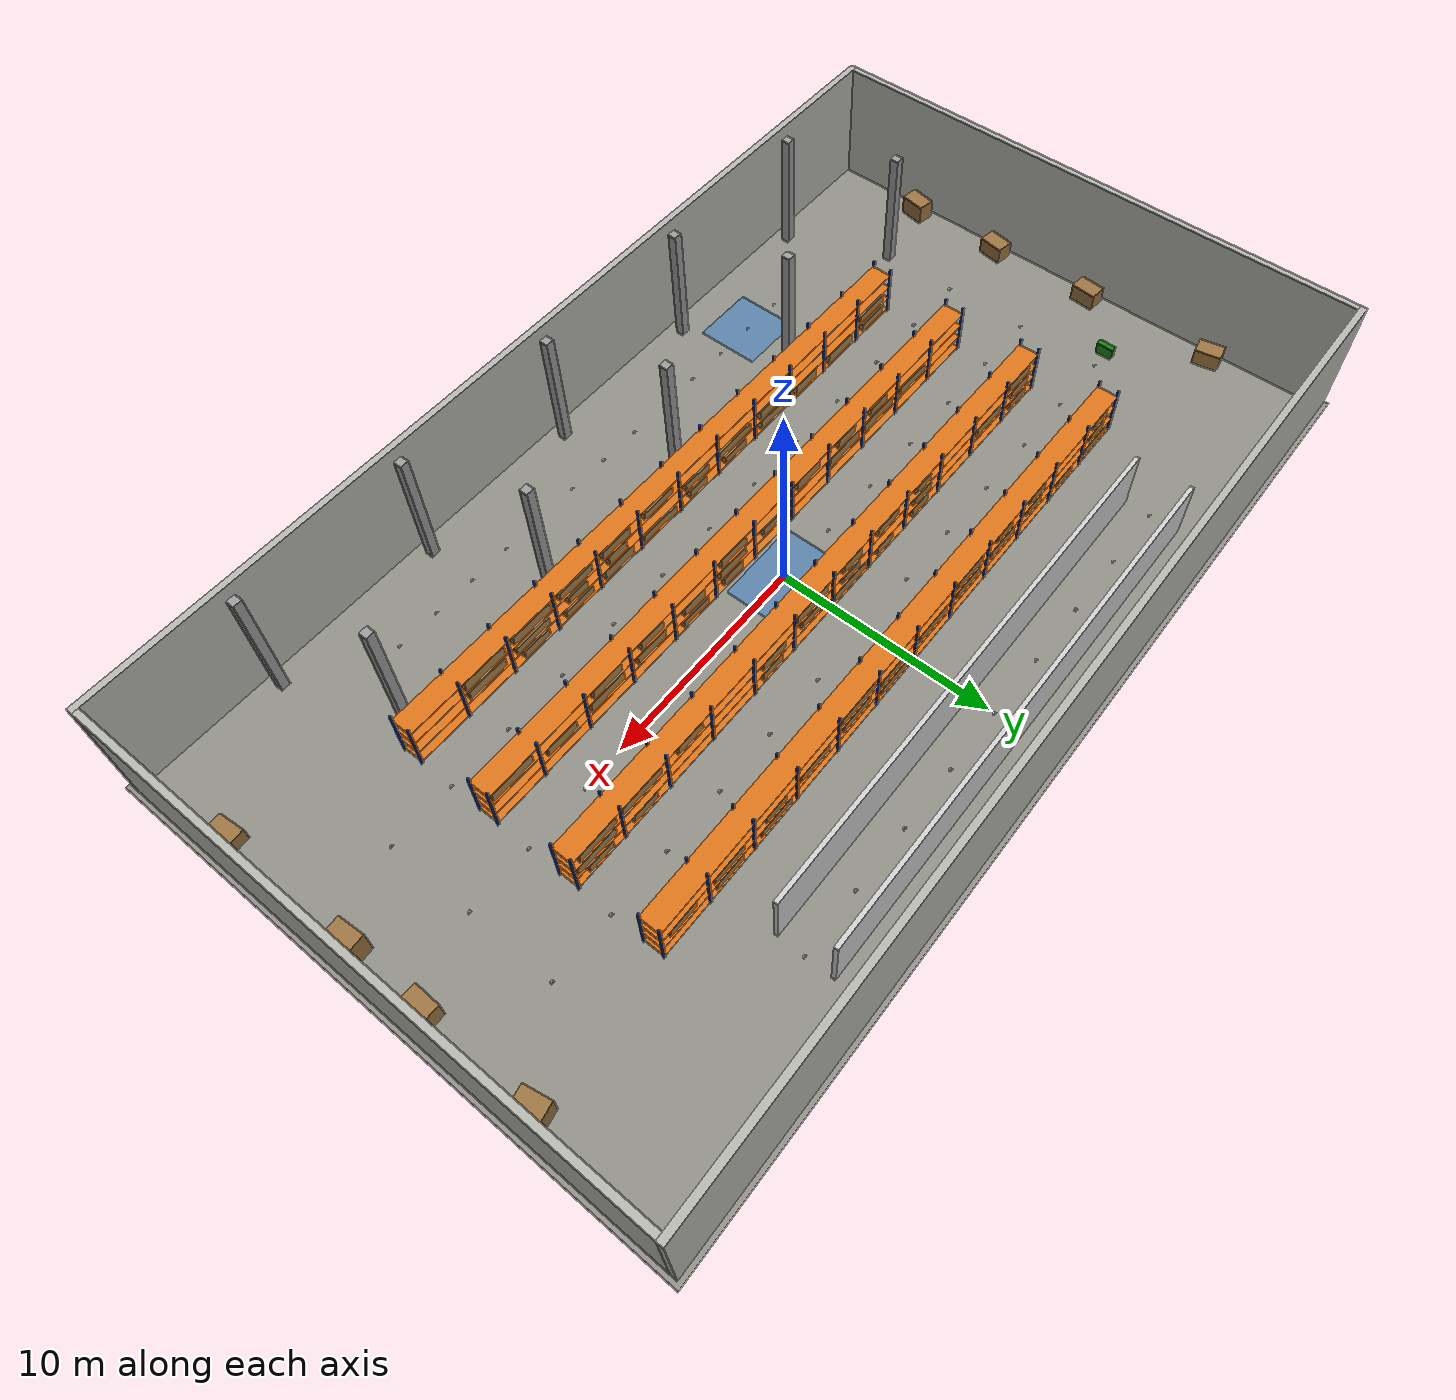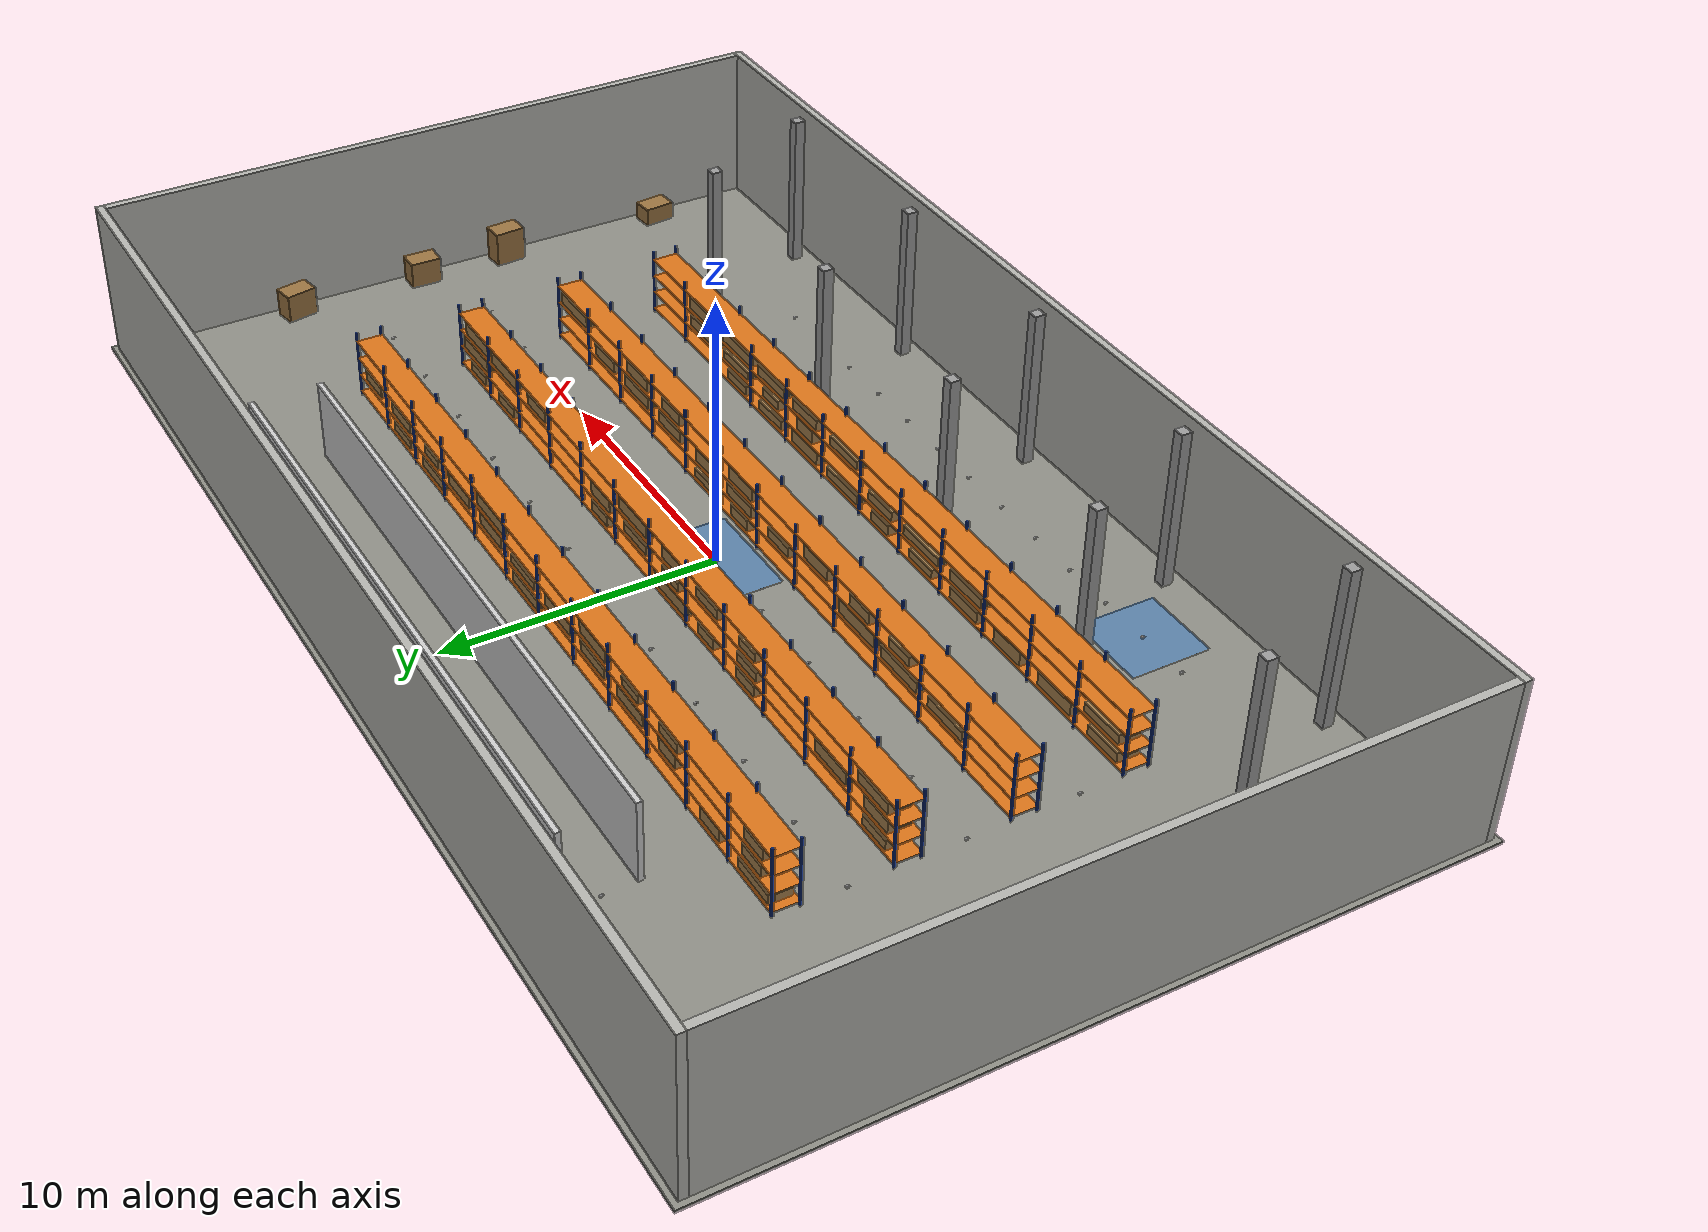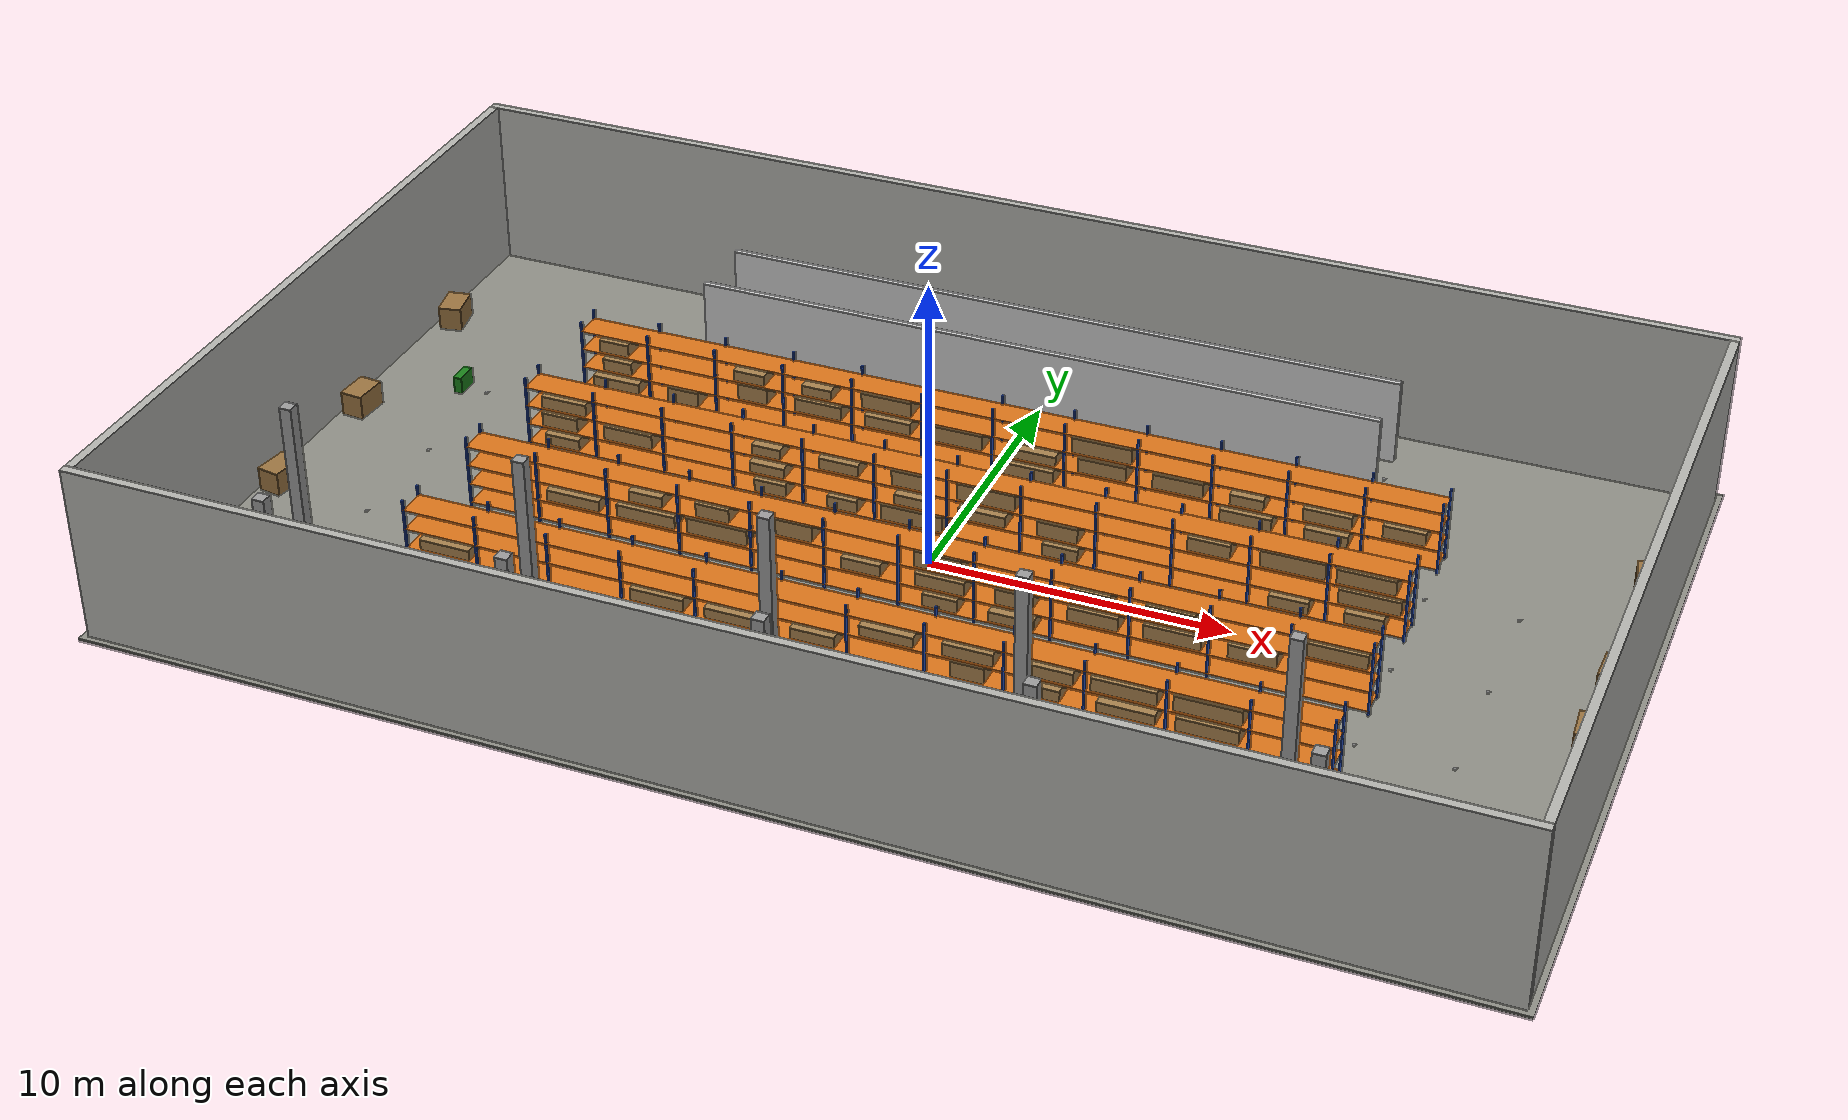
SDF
<?xml version="1.0"?>
<!-- TỰ SINH bởi tools/generate_world.py (Gazebo 11 classic) từ config/layout.yaml (seed=7). Đừng sửa tay. -->
<sdf version="1.6">
  <world name="warehouse">
    <physics name="ode_1ms" default="true" type="ode">
      <max_step_size>0.001</max_step_size>
      <real_time_factor>1.0</real_time_factor>
      <real_time_update_rate>1000</real_time_update_rate>
      <ode><solver><type>quick</type><iters>50</iters></solver></ode>
    </physics>
    <gravity>0 0 -9.81</gravity>
    <scene>
      <ambient>0.04 0.04 0.04 1</ambient>
      <background>0.05 0.05 0.07 1</background>
      <shadows>false</shadows>
      <grid>false</grid>
    </scene>
<light type="point" name="lamp0"><pose>-16.80 4.00 4.0 0 0 0</pose><diffuse>0.9 0.9 0.85 1</diffuse><specular>0.1 0.1 0.1 1</specular><attenuation><range>5.5</range><constant>0.4</constant><linear>0.05</linear><quadratic>0.02</quadratic></attenuation><cast_shadows>false</cast_shadows></light>
<light type="point" name="lamp1"><pose>-8.40 4.00 4.0 0 0 0</pose><diffuse>0.9 0.9 0.85 1</diffuse><specular>0.1 0.1 0.1 1</specular><attenuation><range>5.5</range><constant>0.4</constant><linear>0.05</linear><quadratic>0.02</quadratic></attenuation><cast_shadows>false</cast_shadows></light>
<light type="point" name="lamp2"><pose>0.00 4.00 4.0 0 0 0</pose><diffuse>0.9 0.9 0.85 1</diffuse><specular>0.1 0.1 0.1 1</specular><attenuation><range>5.5</range><constant>0.4</constant><linear>0.05</linear><quadratic>0.02</quadratic></attenuation><cast_shadows>false</cast_shadows></light>
<light type="point" name="lamp3"><pose>8.40 4.00 4.0 0 0 0</pose><diffuse>0.9 0.9 0.85 1</diffuse><specular>0.1 0.1 0.1 1</specular><attenuation><range>5.5</range><constant>0.4</constant><linear>0.05</linear><quadratic>0.02</quadratic></attenuation><cast_shadows>false</cast_shadows></light>
<light type="point" name="lamp4"><pose>16.80 4.00 4.0 0 0 0</pose><diffuse>0.9 0.9 0.85 1</diffuse><specular>0.1 0.1 0.1 1</specular><attenuation><range>5.5</range><constant>0.4</constant><linear>0.05</linear><quadratic>0.02</quadratic></attenuation><cast_shadows>false</cast_shadows></light>
<light type="point" name="lamp5"><pose>-16.80 0.00 4.0 0 0 0</pose><diffuse>0.9 0.9 0.85 1</diffuse><specular>0.1 0.1 0.1 1</specular><attenuation><range>5.5</range><constant>0.4</constant><linear>0.05</linear><quadratic>0.02</quadratic></attenuation><cast_shadows>false</cast_shadows></light>
<light type="point" name="lamp6"><pose>-8.40 0.00 4.0 0 0 0</pose><diffuse>0.9 0.9 0.85 1</diffuse><specular>0.1 0.1 0.1 1</specular><attenuation><range>5.5</range><constant>0.4</constant><linear>0.05</linear><quadratic>0.02</quadratic></attenuation><cast_shadows>false</cast_shadows></light>
<light type="point" name="lamp7"><pose>0.00 0.00 4.0 0 0 0</pose><diffuse>0.9 0.9 0.85 1</diffuse><specular>0.1 0.1 0.1 1</specular><attenuation><range>5.5</range><constant>0.4</constant><linear>0.05</linear><quadratic>0.02</quadratic></attenuation><cast_shadows>false</cast_shadows></light>
<light type="point" name="lamp8"><pose>8.40 0.00 4.0 0 0 0</pose><diffuse>0.9 0.9 0.85 1</diffuse><specular>0.1 0.1 0.1 1</specular><attenuation><range>5.5</range><constant>0.4</constant><linear>0.05</linear><quadratic>0.02</quadratic></attenuation><cast_shadows>false</cast_shadows></light>
<light type="point" name="lamp9"><pose>16.80 0.00 4.0 0 0 0</pose><diffuse>0.9 0.9 0.85 1</diffuse><specular>0.1 0.1 0.1 1</specular><attenuation><range>5.5</range><constant>0.4</constant><linear>0.05</linear><quadratic>0.02</quadratic></attenuation><cast_shadows>false</cast_shadows></light>
<light type="point" name="lamp10"><pose>-16.00 -4.00 4.0 0 0 0</pose><diffuse>0.9 0.9 0.85 1</diffuse><specular>0.1 0.1 0.1 1</specular><attenuation><range>5.5</range><constant>0.4</constant><linear>0.05</linear><quadratic>0.02</quadratic></attenuation><cast_shadows>false</cast_shadows></light>
<light type="point" name="lamp11"><pose>-6.00 -4.00 4.0 0 0 0</pose><diffuse>0.9 0.9 0.85 1</diffuse><specular>0.1 0.1 0.1 1</specular><attenuation><range>5.5</range><constant>0.4</constant><linear>0.05</linear><quadratic>0.02</quadratic></attenuation><cast_shadows>false</cast_shadows></light>
<light type="point" name="lamp12"><pose>-16.80 10.25 4.0 0 0 0</pose><diffuse>0.9 0.9 0.85 1</diffuse><specular>0.1 0.1 0.1 1</specular><attenuation><range>5.5</range><constant>0.4</constant><linear>0.05</linear><quadratic>0.02</quadratic></attenuation><cast_shadows>false</cast_shadows></light>
<light type="point" name="lamp13"><pose>-8.40 10.25 4.0 0 0 0</pose><diffuse>0.9 0.9 0.85 1</diffuse><specular>0.1 0.1 0.1 1</specular><attenuation><range>5.5</range><constant>0.4</constant><linear>0.05</linear><quadratic>0.02</quadratic></attenuation><cast_shadows>false</cast_shadows></light>
<light type="point" name="lamp14"><pose>0.00 10.25 4.0 0 0 0</pose><diffuse>0.9 0.9 0.85 1</diffuse><specular>0.1 0.1 0.1 1</specular><attenuation><range>5.5</range><constant>0.4</constant><linear>0.05</linear><quadratic>0.02</quadratic></attenuation><cast_shadows>false</cast_shadows></light>
<light type="point" name="lamp15"><pose>8.40 10.25 4.0 0 0 0</pose><diffuse>0.9 0.9 0.85 1</diffuse><specular>0.1 0.1 0.1 1</specular><attenuation><range>5.5</range><constant>0.4</constant><linear>0.05</linear><quadratic>0.02</quadratic></attenuation><cast_shadows>false</cast_shadows></light>
<light type="point" name="lamp16"><pose>16.80 10.25 4.0 0 0 0</pose><diffuse>0.9 0.9 0.85 1</diffuse><specular>0.1 0.1 0.1 1</specular><attenuation><range>5.5</range><constant>0.4</constant><linear>0.05</linear><quadratic>0.02</quadratic></attenuation><cast_shadows>false</cast_shadows></light>
<light type="point" name="lamp17"><pose>-16.80 -10.00 4.0 0 0 0</pose><diffuse>0.9 0.9 0.85 1</diffuse><specular>0.1 0.1 0.1 1</specular><attenuation><range>5.5</range><constant>0.4</constant><linear>0.05</linear><quadratic>0.02</quadratic></attenuation><cast_shadows>false</cast_shadows></light>
<light type="point" name="lamp18"><pose>-8.40 -10.00 4.0 0 0 0</pose><diffuse>0.9 0.9 0.85 1</diffuse><specular>0.1 0.1 0.1 1</specular><attenuation><range>5.5</range><constant>0.4</constant><linear>0.05</linear><quadratic>0.02</quadratic></attenuation><cast_shadows>false</cast_shadows></light>
<light type="point" name="lamp19"><pose>0.00 -10.00 4.0 0 0 0</pose><diffuse>0.9 0.9 0.85 1</diffuse><specular>0.1 0.1 0.1 1</specular><attenuation><range>5.5</range><constant>0.4</constant><linear>0.05</linear><quadratic>0.02</quadratic></attenuation><cast_shadows>false</cast_shadows></light>
<light type="point" name="lamp20"><pose>8.40 -10.00 4.0 0 0 0</pose><diffuse>0.9 0.9 0.85 1</diffuse><specular>0.1 0.1 0.1 1</specular><attenuation><range>5.5</range><constant>0.4</constant><linear>0.05</linear><quadratic>0.02</quadratic></attenuation><cast_shadows>false</cast_shadows></light>
<light type="point" name="lamp21"><pose>16.80 -10.00 4.0 0 0 0</pose><diffuse>0.9 0.9 0.85 1</diffuse><specular>0.1 0.1 0.1 1</specular><attenuation><range>5.5</range><constant>0.4</constant><linear>0.05</linear><quadratic>0.02</quadratic></attenuation><cast_shadows>false</cast_shadows></light>
<light type="point" name="lamp22"><pose>-19.50 -4.50 4.0 0 0 0</pose><diffuse>0.9 0.9 0.85 1</diffuse><specular>0.1 0.1 0.1 1</specular><attenuation><range>5.5</range><constant>0.4</constant><linear>0.05</linear><quadratic>0.02</quadratic></attenuation><cast_shadows>false</cast_shadows></light>
<light type="point" name="lamp23"><pose>-19.50 4.50 4.0 0 0 0</pose><diffuse>0.9 0.9 0.85 1</diffuse><specular>0.1 0.1 0.1 1</specular><attenuation><range>5.5</range><constant>0.4</constant><linear>0.05</linear><quadratic>0.02</quadratic></attenuation><cast_shadows>false</cast_shadows></light>
<light type="point" name="lamp24"><pose>19.50 -4.50 4.0 0 0 0</pose><diffuse>0.9 0.9 0.85 1</diffuse><specular>0.1 0.1 0.1 1</specular><attenuation><range>5.5</range><constant>0.4</constant><linear>0.05</linear><quadratic>0.02</quadratic></attenuation><cast_shadows>false</cast_shadows></light>
<light type="point" name="lamp25"><pose>19.50 4.50 4.0 0 0 0</pose><diffuse>0.9 0.9 0.85 1</diffuse><specular>0.1 0.1 0.1 1</specular><attenuation><range>5.5</range><constant>0.4</constant><linear>0.05</linear><quadratic>0.02</quadratic></attenuation><cast_shadows>false</cast_shadows></light>

<model name="warehouse_shell"><static>true</static><link name="link"><visual name="floor_v"><pose>0.0000 0.0000 -0.0500 0 0 0.0000</pose><geometry><box><size>45.0000 27.0000 0.1000</size></box></geometry><material><ambient>0.55 0.55 0.52 1</ambient><diffuse>0.55 0.55 0.52 1</diffuse><specular>0.1 0.1 0.1 1</specular></material></visual><collision name="floor_c"><pose>0.0000 0.0000 -0.0500 0 0 0.0000</pose><geometry><box><size>45.0000 27.0000 0.1000</size></box></geometry><surface><friction><ode><mu>0.9</mu><mu2>0.9</mu2></ode></friction></surface></collision><visual name="wall_n_v"><pose>0.0000 13.1500 3.0000 0 0 0.0000</pose><geometry><box><size>44.6000 0.3000 6.0000</size></box></geometry><material><ambient>0.7 0.7 0.68 1</ambient><diffuse>0.7 0.7 0.68 1</diffuse><specular>0.1 0.1 0.1 1</specular></material></visual><collision name="wall_n_c"><pose>0.0000 13.1500 3.0000 0 0 0.0000</pose><geometry><box><size>44.6000 0.3000 6.0000</size></box></geometry></collision><visual name="wall_s_v"><pose>0.0000 -13.1500 3.0000 0 0 0.0000</pose><geometry><box><size>44.6000 0.3000 6.0000</size></box></geometry><material><ambient>0.7 0.7 0.68 1</ambient><diffuse>0.7 0.7 0.68 1</diffuse><specular>0.1 0.1 0.1 1</specular></material></visual><collision name="wall_s_c"><pose>0.0000 -13.1500 3.0000 0 0 0.0000</pose><geometry><box><size>44.6000 0.3000 6.0000</size></box></geometry></collision><visual name="wall_e_v"><pose>22.1500 0.0000 3.0000 0 0 0.0000</pose><geometry><box><size>0.3000 26.0000 6.0000</size></box></geometry><material><ambient>0.7 0.7 0.68 1</ambient><diffuse>0.7 0.7 0.68 1</diffuse><specular>0.1 0.1 0.1 1</specular></material></visual><collision name="wall_e_c"><pose>22.1500 0.0000 3.0000 0 0 0.0000</pose><geometry><box><size>0.3000 26.0000 6.0000</size></box></geometry></collision><visual name="wall_w_v"><pose>-22.1500 0.0000 3.0000 0 0 0.0000</pose><geometry><box><size>0.3000 26.0000 6.0000</size></box></geometry><material><ambient>0.7 0.7 0.68 1</ambient><diffuse>0.7 0.7 0.68 1</diffuse><specular>0.1 0.1 0.1 1</specular></material></visual><collision name="wall_w_c"><pose>-22.1500 0.0000 3.0000 0 0 0.0000</pose><geometry><box><size>0.3000 26.0000 6.0000</size></box></geometry></collision><visual name="slip_slip_patch_B_v"><pose>0.0000 0.0000 0.0005 0 0 0.0000</pose><geometry><box><size>4.0000 2.8000 0.0010</size></box></geometry><material><ambient>0.35 0.5 0.65 1</ambient><diffuse>0.35 0.5 0.65 1</diffuse><specular>0.1 0.1 0.1 1</specular></material></visual><collision name="slip_slip_patch_B_c"><pose>0.0000 0.0000 0.0005 0 0 0.0000</pose><geometry><box><size>4.0000 2.8000 0.0010</size></box></geometry><surface><friction><ode><mu>0.06</mu><mu2>0.06</mu2></ode></friction></surface></collision><visual name="slip_slip_patch_spin_v"><pose>-10.0000 -10.0000 0.0005 0 0 0.0000</pose><geometry><box><size>3.0000 3.0000 0.0010</size></box></geometry><material><ambient>0.35 0.5 0.65 1</ambient><diffuse>0.35 0.5 0.65 1</diffuse><specular>0.1 0.1 0.1 1</specular></material></visual><collision name="slip_slip_patch_spin_c"><pose>-10.0000 -10.0000 0.0005 0 0 0.0000</pose><geometry><box><size>3.0000 3.0000 0.0010</size></box></geometry><surface><friction><ode><mu>0.06</mu><mu2>0.06</mu2></ode></friction></surface></collision><visual name="qr0_v"><pose>-18.0000 4.0000 0.0015 0 0 0.0000</pose><geometry><box><size>0.1200 0.1200 0.0010</size></box></geometry><material><ambient>0.02 0.02 0.02 1</ambient><diffuse>0.02 0.02 0.02 1</diffuse><specular>0.1 0.1 0.1 1</specular></material></visual><visual name="qr0_in_v"><pose>-18.0000 4.0000 0.0021 0 0 0.0000</pose><geometry><box><size>0.0480 0.0480 0.0010</size></box></geometry><material><ambient>0.95 0.95 0.95 1</ambient><diffuse>0.95 0.95 0.95 1</diffuse><specular>0.1 0.1 0.1 1</specular></material></visual><visual name="qr1_v"><pose>-15.0000 4.0000 0.0015 0 0 0.0000</pose><geometry><box><size>0.1200 0.1200 0.0010</size></box></geometry><material><ambient>0.02 0.02 0.02 1</ambient><diffuse>0.02 0.02 0.02 1</diffuse><specular>0.1 0.1 0.1 1</specular></material></visual><visual name="qr1_in_v"><pose>-15.0000 4.0000 0.0021 0 0 0.0000</pose><geometry><box><size>0.0480 0.0480 0.0010</size></box></geometry><material><ambient>0.95 0.95 0.95 1</ambient><diffuse>0.95 0.95 0.95 1</diffuse><specular>0.1 0.1 0.1 1</specular></material></visual><visual name="qr2_v"><pose>-12.0000 4.0000 0.0015 0 0 0.0000</pose><geometry><box><size>0.1200 0.1200 0.0010</size></box></geometry><material><ambient>0.02 0.02 0.02 1</ambient><diffuse>0.02 0.02 0.02 1</diffuse><specular>0.1 0.1 0.1 1</specular></material></visual><visual name="qr2_in_v"><pose>-12.0000 4.0000 0.0021 0 0 0.0000</pose><geometry><box><size>0.0480 0.0480 0.0010</size></box></geometry><material><ambient>0.95 0.95 0.95 1</ambient><diffuse>0.95 0.95 0.95 1</diffuse><specular>0.1 0.1 0.1 1</specular></material></visual><visual name="qr3_v"><pose>-9.0000 4.0000 0.0015 0 0 0.0000</pose><geometry><box><size>0.1200 0.1200 0.0010</size></box></geometry><material><ambient>0.02 0.02 0.02 1</ambient><diffuse>0.02 0.02 0.02 1</diffuse><specular>0.1 0.1 0.1 1</specular></material></visual><visual name="qr3_in_v"><pose>-9.0000 4.0000 0.0021 0 0 0.0000</pose><geometry><box><size>0.0480 0.0480 0.0010</size></box></geometry><material><ambient>0.95 0.95 0.95 1</ambient><diffuse>0.95 0.95 0.95 1</diffuse><specular>0.1 0.1 0.1 1</specular></material></visual><visual name="qr4_v"><pose>-6.0000 4.0000 0.0015 0 0 0.0000</pose><geometry><box><size>0.1200 0.1200 0.0010</size></box></geometry><material><ambient>0.02 0.02 0.02 1</ambient><diffuse>0.02 0.02 0.02 1</diffuse><specular>0.1 0.1 0.1 1</specular></material></visual><visual name="qr4_in_v"><pose>-6.0000 4.0000 0.0021 0 0 0.0000</pose><geometry><box><size>0.0480 0.0480 0.0010</size></box></geometry><material><ambient>0.95 0.95 0.95 1</ambient><diffuse>0.95 0.95 0.95 1</diffuse><specular>0.1 0.1 0.1 1</specular></material></visual><visual name="qr5_v"><pose>-3.0000 4.0000 0.0015 0 0 0.0000</pose><geometry><box><size>0.1200 0.1200 0.0010</size></box></geometry><material><ambient>0.02 0.02 0.02 1</ambient><diffuse>0.02 0.02 0.02 1</diffuse><specular>0.1 0.1 0.1 1</specular></material></visual><visual name="qr5_in_v"><pose>-3.0000 4.0000 0.0021 0 0 0.0000</pose><geometry><box><size>0.0480 0.0480 0.0010</size></box></geometry><material><ambient>0.95 0.95 0.95 1</ambient><diffuse>0.95 0.95 0.95 1</diffuse><specular>0.1 0.1 0.1 1</specular></material></visual><visual name="qr6_v"><pose>0.0000 4.0000 0.0015 0 0 0.0000</pose><geometry><box><size>0.1200 0.1200 0.0010</size></box></geometry><material><ambient>0.02 0.02 0.02 1</ambient><diffuse>0.02 0.02 0.02 1</diffuse><specular>0.1 0.1 0.1 1</specular></material></visual><visual name="qr6_in_v"><pose>0.0000 4.0000 0.0021 0 0 0.0000</pose><geometry><box><size>0.0480 0.0480 0.0010</size></box></geometry><material><ambient>0.95 0.95 0.95 1</ambient><diffuse>0.95 0.95 0.95 1</diffuse><specular>0.1 0.1 0.1 1</specular></material></visual><visual name="qr7_v"><pose>3.0000 4.0000 0.0015 0 0 0.0000</pose><geometry><box><size>0.1200 0.1200 0.0010</size></box></geometry><material><ambient>0.02 0.02 0.02 1</ambient><diffuse>0.02 0.02 0.02 1</diffuse><specular>0.1 0.1 0.1 1</specular></material></visual><visual name="qr7_in_v"><pose>3.0000 4.0000 0.0021 0 0 0.0000</pose><geometry><box><size>0.0480 0.0480 0.0010</size></box></geometry><material><ambient>0.95 0.95 0.95 1</ambient><diffuse>0.95 0.95 0.95 1</diffuse><specular>0.1 0.1 0.1 1</specular></material></visual><visual name="qr8_v"><pose>6.0000 4.0000 0.0015 0 0 0.0000</pose><geometry><box><size>0.1200 0.1200 0.0010</size></box></geometry><material><ambient>0.02 0.02 0.02 1</ambient><diffuse>0.02 0.02 0.02 1</diffuse><specular>0.1 0.1 0.1 1</specular></material></visual><visual name="qr8_in_v"><pose>6.0000 4.0000 0.0021 0 0 0.0000</pose><geometry><box><size>0.0480 0.0480 0.0010</size></box></geometry><material><ambient>0.95 0.95 0.95 1</ambient><diffuse>0.95 0.95 0.95 1</diffuse><specular>0.1 0.1 0.1 1</specular></material></visual><visual name="qr9_v"><pose>9.0000 4.0000 0.0015 0 0 0.0000</pose><geometry><box><size>0.1200 0.1200 0.0010</size></box></geometry><material><ambient>0.02 0.02 0.02 1</ambient><diffuse>0.02 0.02 0.02 1</diffuse><specular>0.1 0.1 0.1 1</specular></material></visual><visual name="qr9_in_v"><pose>9.0000 4.0000 0.0021 0 0 0.0000</pose><geometry><box><size>0.0480 0.0480 0.0010</size></box></geometry><material><ambient>0.95 0.95 0.95 1</ambient><diffuse>0.95 0.95 0.95 1</diffuse><specular>0.1 0.1 0.1 1</specular></material></visual><visual name="qr10_v"><pose>12.0000 4.0000 0.0015 0 0 0.0000</pose><geometry><box><size>0.1200 0.1200 0.0010</size></box></geometry><material><ambient>0.02 0.02 0.02 1</ambient><diffuse>0.02 0.02 0.02 1</diffuse><specular>0.1 0.1 0.1 1</specular></material></visual><visual name="qr10_in_v"><pose>12.0000 4.0000 0.0021 0 0 0.0000</pose><geometry><box><size>0.0480 0.0480 0.0010</size></box></geometry><material><ambient>0.95 0.95 0.95 1</ambient><diffuse>0.95 0.95 0.95 1</diffuse><specular>0.1 0.1 0.1 1</specular></material></visual><visual name="qr11_v"><pose>15.0000 4.0000 0.0015 0 0 0.0000</pose><geometry><box><size>0.1200 0.1200 0.0010</size></box></geometry><material><ambient>0.02 0.02 0.02 1</ambient><diffuse>0.02 0.02 0.02 1</diffuse><specular>0.1 0.1 0.1 1</specular></material></visual><visual name="qr11_in_v"><pose>15.0000 4.0000 0.0021 0 0 0.0000</pose><geometry><box><size>0.0480 0.0480 0.0010</size></box></geometry><material><ambient>0.95 0.95 0.95 1</ambient><diffuse>0.95 0.95 0.95 1</diffuse><specular>0.1 0.1 0.1 1</specular></material></visual><visual name="qr12_v"><pose>18.0000 4.0000 0.0015 0 0 0.0000</pose><geometry><box><size>0.1200 0.1200 0.0010</size></box></geometry><material><ambient>0.02 0.02 0.02 1</ambient><diffuse>0.02 0.02 0.02 1</diffuse><specular>0.1 0.1 0.1 1</specular></material></visual><visual name="qr12_in_v"><pose>18.0000 4.0000 0.0021 0 0 0.0000</pose><geometry><box><size>0.0480 0.0480 0.0010</size></box></geometry><material><ambient>0.95 0.95 0.95 1</ambient><diffuse>0.95 0.95 0.95 1</diffuse><specular>0.1 0.1 0.1 1</specular></material></visual><visual name="qr13_v"><pose>-18.0000 0.0000 0.0015 0 0 0.0000</pose><geometry><box><size>0.1200 0.1200 0.0010</size></box></geometry><material><ambient>0.02 0.02 0.02 1</ambient><diffuse>0.02 0.02 0.02 1</diffuse><specular>0.1 0.1 0.1 1</specular></material></visual><visual name="qr13_in_v"><pose>-18.0000 0.0000 0.0021 0 0 0.0000</pose><geometry><box><size>0.0480 0.0480 0.0010</size></box></geometry><material><ambient>0.95 0.95 0.95 1</ambient><diffuse>0.95 0.95 0.95 1</diffuse><specular>0.1 0.1 0.1 1</specular></material></visual><visual name="qr14_v"><pose>-15.0000 0.0000 0.0015 0 0 0.0000</pose><geometry><box><size>0.1200 0.1200 0.0010</size></box></geometry><material><ambient>0.02 0.02 0.02 1</ambient><diffuse>0.02 0.02 0.02 1</diffuse><specular>0.1 0.1 0.1 1</specular></material></visual><visual name="qr14_in_v"><pose>-15.0000 0.0000 0.0021 0 0 0.0000</pose><geometry><box><size>0.0480 0.0480 0.0010</size></box></geometry><material><ambient>0.95 0.95 0.95 1</ambient><diffuse>0.95 0.95 0.95 1</diffuse><specular>0.1 0.1 0.1 1</specular></material></visual><visual name="qr15_v"><pose>-12.0000 0.0000 0.0015 0 0 0.0000</pose><geometry><box><size>0.1200 0.1200 0.0010</size></box></geometry><material><ambient>0.02 0.02 0.02 1</ambient><diffuse>0.02 0.02 0.02 1</diffuse><specular>0.1 0.1 0.1 1</specular></material></visual><visual name="qr15_in_v"><pose>-12.0000 0.0000 0.0021 0 0 0.0000</pose><geometry><box><size>0.0480 0.0480 0.0010</size></box></geometry><material><ambient>0.95 0.95 0.95 1</ambient><diffuse>0.95 0.95 0.95 1</diffuse><specular>0.1 0.1 0.1 1</specular></material></visual><visual name="qr16_v"><pose>-9.0000 0.0000 0.0015 0 0 0.0000</pose><geometry><box><size>0.1200 0.1200 0.0010</size></box></geometry><material><ambient>0.02 0.02 0.02 1</ambient><diffuse>0.02 0.02 0.02 1</diffuse><specular>0.1 0.1 0.1 1</specular></material></visual><visual name="qr16_in_v"><pose>-9.0000 0.0000 0.0021 0 0 0.0000</pose><geometry><box><size>0.0480 0.0480 0.0010</size></box></geometry><material><ambient>0.95 0.95 0.95 1</ambient><diffuse>0.95 0.95 0.95 1</diffuse><specular>0.1 0.1 0.1 1</specular></material></visual><visual name="qr17_v"><pose>-6.0000 0.0000 0.0015 0 0 0.0000</pose><geometry><box><size>0.1200 0.1200 0.0010</size></box></geometry><material><ambient>0.02 0.02 0.02 1</ambient><diffuse>0.02 0.02 0.02 1</diffuse><specular>0.1 0.1 0.1 1</specular></material></visual><visual name="qr17_in_v"><pose>-6.0000 0.0000 0.0021 0 0 0.0000</pose><geometry><box><size>0.0480 0.0480 0.0010</size></box></geometry><material><ambient>0.95 0.95 0.95 1</ambient><diffuse>0.95 0.95 0.95 1</diffuse><specular>0.1 0.1 0.1 1</specular></material></visual><visual name="qr18_v"><pose>-3.0000 0.0000 0.0015 0 0 0.0000</pose><geometry><box><size>0.1200 0.1200 0.0010</size></box></geometry><material><ambient>0.02 0.02 0.02 1</ambient><diffuse>0.02 0.02 0.02 1</diffuse><specular>0.1 0.1 0.1 1</specular></material></visual><visual name="qr18_in_v"><pose>-3.0000 0.0000 0.0021 0 0 0.0000</pose><geometry><box><size>0.0480 0.0480 0.0010</size></box></geometry><material><ambient>0.95 0.95 0.95 1</ambient><diffuse>0.95 0.95 0.95 1</diffuse><specular>0.1 0.1 0.1 1</specular></material></visual><visual name="qr19_v"><pose>0.0000 0.0000 0.0015 0 0 0.0000</pose><geometry><box><size>0.1200 0.1200 0.0010</size></box></geometry><material><ambient>0.02 0.02 0.02 1</ambient><diffuse>0.02 0.02 0.02 1</diffuse><specular>0.1 0.1 0.1 1</specular></material></visual><visual name="qr19_in_v"><pose>0.0000 0.0000 0.0021 0 0 0.0000</pose><geometry><box><size>0.0480 0.0480 0.0010</size></box></geometry><material><ambient>0.95 0.95 0.95 1</ambient><diffuse>0.95 0.95 0.95 1</diffuse><specular>0.1 0.1 0.1 1</specular></material></visual><visual name="qr20_v"><pose>3.0000 0.0000 0.0015 0 0 0.0000</pose><geometry><box><size>0.1200 0.1200 0.0010</size></box></geometry><material><ambient>0.02 0.02 0.02 1</ambient><diffuse>0.02 0.02 0.02 1</diffuse><specular>0.1 0.1 0.1 1</specular></material></visual><visual name="qr20_in_v"><pose>3.0000 0.0000 0.0021 0 0 0.0000</pose><geometry><box><size>0.0480 0.0480 0.0010</size></box></geometry><material><ambient>0.95 0.95 0.95 1</ambient><diffuse>0.95 0.95 0.95 1</diffuse><specular>0.1 0.1 0.1 1</specular></material></visual><visual name="qr21_v"><pose>6.0000 0.0000 0.0015 0 0 0.0000</pose><geometry><box><size>0.1200 0.1200 0.0010</size></box></geometry><material><ambient>0.02 0.02 0.02 1</ambient><diffuse>0.02 0.02 0.02 1</diffuse><specular>0.1 0.1 0.1 1</specular></material></visual><visual name="qr21_in_v"><pose>6.0000 0.0000 0.0021 0 0 0.0000</pose><geometry><box><size>0.0480 0.0480 0.0010</size></box></geometry><material><ambient>0.95 0.95 0.95 1</ambient><diffuse>0.95 0.95 0.95 1</diffuse><specular>0.1 0.1 0.1 1</specular></material></visual><visual name="qr22_v"><pose>9.0000 0.0000 0.0015 0 0 0.0000</pose><geometry><box><size>0.1200 0.1200 0.0010</size></box></geometry><material><ambient>0.02 0.02 0.02 1</ambient><diffuse>0.02 0.02 0.02 1</diffuse><specular>0.1 0.1 0.1 1</specular></material></visual><visual name="qr22_in_v"><pose>9.0000 0.0000 0.0021 0 0 0.0000</pose><geometry><box><size>0.0480 0.0480 0.0010</size></box></geometry><material><ambient>0.95 0.95 0.95 1</ambient><diffuse>0.95 0.95 0.95 1</diffuse><specular>0.1 0.1 0.1 1</specular></material></visual><visual name="qr23_v"><pose>12.0000 0.0000 0.0015 0 0 0.0000</pose><geometry><box><size>0.1200 0.1200 0.0010</size></box></geometry><material><ambient>0.02 0.02 0.02 1</ambient><diffuse>0.02 0.02 0.02 1</diffuse><specular>0.1 0.1 0.1 1</specular></material></visual><visual name="qr23_in_v"><pose>12.0000 0.0000 0.0021 0 0 0.0000</pose><geometry><box><size>0.0480 0.0480 0.0010</size></box></geometry><material><ambient>0.95 0.95 0.95 1</ambient><diffuse>0.95 0.95 0.95 1</diffuse><specular>0.1 0.1 0.1 1</specular></material></visual><visual name="qr24_v"><pose>15.0000 0.0000 0.0015 0 0 0.0000</pose><geometry><box><size>0.1200 0.1200 0.0010</size></box></geometry><material><ambient>0.02 0.02 0.02 1</ambient><diffuse>0.02 0.02 0.02 1</diffuse><specular>0.1 0.1 0.1 1</specular></material></visual><visual name="qr24_in_v"><pose>15.0000 0.0000 0.0021 0 0 0.0000</pose><geometry><box><size>0.0480 0.0480 0.0010</size></box></geometry><material><ambient>0.95 0.95 0.95 1</ambient><diffuse>0.95 0.95 0.95 1</diffuse><specular>0.1 0.1 0.1 1</specular></material></visual><visual name="qr25_v"><pose>18.0000 0.0000 0.0015 0 0 0.0000</pose><geometry><box><size>0.1200 0.1200 0.0010</size></box></geometry><material><ambient>0.02 0.02 0.02 1</ambient><diffuse>0.02 0.02 0.02 1</diffuse><specular>0.1 0.1 0.1 1</specular></material></visual><visual name="qr25_in_v"><pose>18.0000 0.0000 0.0021 0 0 0.0000</pose><geometry><box><size>0.0480 0.0480 0.0010</size></box></geometry><material><ambient>0.95 0.95 0.95 1</ambient><diffuse>0.95 0.95 0.95 1</diffuse><specular>0.1 0.1 0.1 1</specular></material></visual><visual name="qr26_v"><pose>-18.0000 -4.0000 0.0015 0 0 0.0000</pose><geometry><box><size>0.1200 0.1200 0.0010</size></box></geometry><material><ambient>0.02 0.02 0.02 1</ambient><diffuse>0.02 0.02 0.02 1</diffuse><specular>0.1 0.1 0.1 1</specular></material></visual><visual name="qr26_in_v"><pose>-18.0000 -4.0000 0.0021 0 0 0.0000</pose><geometry><box><size>0.0480 0.0480 0.0010</size></box></geometry><material><ambient>0.95 0.95 0.95 1</ambient><diffuse>0.95 0.95 0.95 1</diffuse><specular>0.1 0.1 0.1 1</specular></material></visual><visual name="qr27_v"><pose>-15.0000 -4.0000 0.0015 0 0 0.0000</pose><geometry><box><size>0.1200 0.1200 0.0010</size></box></geometry><material><ambient>0.02 0.02 0.02 1</ambient><diffuse>0.02 0.02 0.02 1</diffuse><specular>0.1 0.1 0.1 1</specular></material></visual><visual name="qr27_in_v"><pose>-15.0000 -4.0000 0.0021 0 0 0.0000</pose><geometry><box><size>0.0480 0.0480 0.0010</size></box></geometry><material><ambient>0.95 0.95 0.95 1</ambient><diffuse>0.95 0.95 0.95 1</diffuse><specular>0.1 0.1 0.1 1</specular></material></visual><visual name="qr28_v"><pose>-12.0000 -4.0000 0.0015 0 0 0.0000</pose><geometry><box><size>0.1200 0.1200 0.0010</size></box></geometry><material><ambient>0.02 0.02 0.02 1</ambient><diffuse>0.02 0.02 0.02 1</diffuse><specular>0.1 0.1 0.1 1</specular></material></visual><visual name="qr28_in_v"><pose>-12.0000 -4.0000 0.0021 0 0 0.0000</pose><geometry><box><size>0.0480 0.0480 0.0010</size></box></geometry><material><ambient>0.95 0.95 0.95 1</ambient><diffuse>0.95 0.95 0.95 1</diffuse><specular>0.1 0.1 0.1 1</specular></material></visual><visual name="qr29_v"><pose>-9.0000 -4.0000 0.0015 0 0 0.0000</pose><geometry><box><size>0.1200 0.1200 0.0010</size></box></geometry><material><ambient>0.02 0.02 0.02 1</ambient><diffuse>0.02 0.02 0.02 1</diffuse><specular>0.1 0.1 0.1 1</specular></material></visual><visual name="qr29_in_v"><pose>-9.0000 -4.0000 0.0021 0 0 0.0000</pose><geometry><box><size>0.0480 0.0480 0.0010</size></box></geometry><material><ambient>0.95 0.95 0.95 1</ambient><diffuse>0.95 0.95 0.95 1</diffuse><specular>0.1 0.1 0.1 1</specular></material></visual><visual name="qr30_v"><pose>-6.0000 -4.0000 0.0015 0 0 0.0000</pose><geometry><box><size>0.1200 0.1200 0.0010</size></box></geometry><material><ambient>0.02 0.02 0.02 1</ambient><diffuse>0.02 0.02 0.02 1</diffuse><specular>0.1 0.1 0.1 1</specular></material></visual><visual name="qr30_in_v"><pose>-6.0000 -4.0000 0.0021 0 0 0.0000</pose><geometry><box><size>0.0480 0.0480 0.0010</size></box></geometry><material><ambient>0.95 0.95 0.95 1</ambient><diffuse>0.95 0.95 0.95 1</diffuse><specular>0.1 0.1 0.1 1</specular></material></visual><visual name="qr31_v"><pose>-3.0000 -4.0000 0.0015 0 0 0.0000</pose><geometry><box><size>0.1200 0.1200 0.0010</size></box></geometry><material><ambient>0.02 0.02 0.02 1</ambient><diffuse>0.02 0.02 0.02 1</diffuse><specular>0.1 0.1 0.1 1</specular></material></visual><visual name="qr31_in_v"><pose>-3.0000 -4.0000 0.0021 0 0 0.0000</pose><geometry><box><size>0.0480 0.0480 0.0010</size></box></geometry><material><ambient>0.95 0.95 0.95 1</ambient><diffuse>0.95 0.95 0.95 1</diffuse><specular>0.1 0.1 0.1 1</specular></material></visual><visual name="qr32_v"><pose>0.0000 -4.0000 0.0015 0 0 0.0000</pose><geometry><box><size>0.1200 0.1200 0.0010</size></box></geometry><material><ambient>0.02 0.02 0.02 1</ambient><diffuse>0.02 0.02 0.02 1</diffuse><specular>0.1 0.1 0.1 1</specular></material></visual><visual name="qr32_in_v"><pose>0.0000 -4.0000 0.0021 0 0 0.0000</pose><geometry><box><size>0.0480 0.0480 0.0010</size></box></geometry><material><ambient>0.95 0.95 0.95 1</ambient><diffuse>0.95 0.95 0.95 1</diffuse><specular>0.1 0.1 0.1 1</specular></material></visual><visual name="qr33_v"><pose>3.0000 -4.0000 0.0015 0 0 0.0000</pose><geometry><box><size>0.1200 0.1200 0.0010</size></box></geometry><material><ambient>0.02 0.02 0.02 1</ambient><diffuse>0.02 0.02 0.02 1</diffuse><specular>0.1 0.1 0.1 1</specular></material></visual><visual name="qr33_in_v"><pose>3.0000 -4.0000 0.0021 0 0 0.0000</pose><geometry><box><size>0.0480 0.0480 0.0010</size></box></geometry><material><ambient>0.95 0.95 0.95 1</ambient><diffuse>0.95 0.95 0.95 1</diffuse><specular>0.1 0.1 0.1 1</specular></material></visual><visual name="qr34_v"><pose>6.0000 -4.0000 0.0015 0 0 0.0000</pose><geometry><box><size>0.1200 0.1200 0.0010</size></box></geometry><material><ambient>0.02 0.02 0.02 1</ambient><diffuse>0.02 0.02 0.02 1</diffuse><specular>0.1 0.1 0.1 1</specular></material></visual><visual name="qr34_in_v"><pose>6.0000 -4.0000 0.0021 0 0 0.0000</pose><geometry><box><size>0.0480 0.0480 0.0010</size></box></geometry><material><ambient>0.95 0.95 0.95 1</ambient><diffuse>0.95 0.95 0.95 1</diffuse><specular>0.1 0.1 0.1 1</specular></material></visual><visual name="qr35_v"><pose>9.0000 -4.0000 0.0015 0 0 0.0000</pose><geometry><box><size>0.1200 0.1200 0.0010</size></box></geometry><material><ambient>0.02 0.02 0.02 1</ambient><diffuse>0.02 0.02 0.02 1</diffuse><specular>0.1 0.1 0.1 1</specular></material></visual><visual name="qr35_in_v"><pose>9.0000 -4.0000 0.0021 0 0 0.0000</pose><geometry><box><size>0.0480 0.0480 0.0010</size></box></geometry><material><ambient>0.95 0.95 0.95 1</ambient><diffuse>0.95 0.95 0.95 1</diffuse><specular>0.1 0.1 0.1 1</specular></material></visual><visual name="qr36_v"><pose>12.0000 -4.0000 0.0015 0 0 0.0000</pose><geometry><box><size>0.1200 0.1200 0.0010</size></box></geometry><material><ambient>0.02 0.02 0.02 1</ambient><diffuse>0.02 0.02 0.02 1</diffuse><specular>0.1 0.1 0.1 1</specular></material></visual><visual name="qr36_in_v"><pose>12.0000 -4.0000 0.0021 0 0 0.0000</pose><geometry><box><size>0.0480 0.0480 0.0010</size></box></geometry><material><ambient>0.95 0.95 0.95 1</ambient><diffuse>0.95 0.95 0.95 1</diffuse><specular>0.1 0.1 0.1 1</specular></material></visual><visual name="qr37_v"><pose>15.0000 -4.0000 0.0015 0 0 0.0000</pose><geometry><box><size>0.1200 0.1200 0.0010</size></box></geometry><material><ambient>0.02 0.02 0.02 1</ambient><diffuse>0.02 0.02 0.02 1</diffuse><specular>0.1 0.1 0.1 1</specular></material></visual><visual name="qr37_in_v"><pose>15.0000 -4.0000 0.0021 0 0 0.0000</pose><geometry><box><size>0.0480 0.0480 0.0010</size></box></geometry><material><ambient>0.95 0.95 0.95 1</ambient><diffuse>0.95 0.95 0.95 1</diffuse><specular>0.1 0.1 0.1 1</specular></material></visual><visual name="qr38_v"><pose>18.0000 -4.0000 0.0015 0 0 0.0000</pose><geometry><box><size>0.1200 0.1200 0.0010</size></box></geometry><material><ambient>0.02 0.02 0.02 1</ambient><diffuse>0.02 0.02 0.02 1</diffuse><specular>0.1 0.1 0.1 1</specular></material></visual><visual name="qr38_in_v"><pose>18.0000 -4.0000 0.0021 0 0 0.0000</pose><geometry><box><size>0.0480 0.0480 0.0010</size></box></geometry><material><ambient>0.95 0.95 0.95 1</ambient><diffuse>0.95 0.95 0.95 1</diffuse><specular>0.1 0.1 0.1 1</specular></material></visual><visual name="qr39_v"><pose>-12.0000 10.2500 0.0015 0 0 0.0000</pose><geometry><box><size>0.1200 0.1200 0.0010</size></box></geometry><material><ambient>0.02 0.02 0.02 1</ambient><diffuse>0.02 0.02 0.02 1</diffuse><specular>0.1 0.1 0.1 1</specular></material></visual><visual name="qr39_in_v"><pose>-12.0000 10.2500 0.0021 0 0 0.0000</pose><geometry><box><size>0.0480 0.0480 0.0010</size></box></geometry><material><ambient>0.95 0.95 0.95 1</ambient><diffuse>0.95 0.95 0.95 1</diffuse><specular>0.1 0.1 0.1 1</specular></material></visual><visual name="qr40_v"><pose>-9.0000 10.2500 0.0015 0 0 0.0000</pose><geometry><box><size>0.1200 0.1200 0.0010</size></box></geometry><material><ambient>0.02 0.02 0.02 1</ambient><diffuse>0.02 0.02 0.02 1</diffuse><specular>0.1 0.1 0.1 1</specular></material></visual><visual name="qr40_in_v"><pose>-9.0000 10.2500 0.0021 0 0 0.0000</pose><geometry><box><size>0.0480 0.0480 0.0010</size></box></geometry><material><ambient>0.95 0.95 0.95 1</ambient><diffuse>0.95 0.95 0.95 1</diffuse><specular>0.1 0.1 0.1 1</specular></material></visual><visual name="qr41_v"><pose>-6.0000 10.2500 0.0015 0 0 0.0000</pose><geometry><box><size>0.1200 0.1200 0.0010</size></box></geometry><material><ambient>0.02 0.02 0.02 1</ambient><diffuse>0.02 0.02 0.02 1</diffuse><specular>0.1 0.1 0.1 1</specular></material></visual><visual name="qr41_in_v"><pose>-6.0000 10.2500 0.0021 0 0 0.0000</pose><geometry><box><size>0.0480 0.0480 0.0010</size></box></geometry><material><ambient>0.95 0.95 0.95 1</ambient><diffuse>0.95 0.95 0.95 1</diffuse><specular>0.1 0.1 0.1 1</specular></material></visual><visual name="qr42_v"><pose>-3.0000 10.2500 0.0015 0 0 0.0000</pose><geometry><box><size>0.1200 0.1200 0.0010</size></box></geometry><material><ambient>0.02 0.02 0.02 1</ambient><diffuse>0.02 0.02 0.02 1</diffuse><specular>0.1 0.1 0.1 1</specular></material></visual><visual name="qr42_in_v"><pose>-3.0000 10.2500 0.0021 0 0 0.0000</pose><geometry><box><size>0.0480 0.0480 0.0010</size></box></geometry><material><ambient>0.95 0.95 0.95 1</ambient><diffuse>0.95 0.95 0.95 1</diffuse><specular>0.1 0.1 0.1 1</specular></material></visual><visual name="qr43_v"><pose>0.0000 10.2500 0.0015 0 0 0.0000</pose><geometry><box><size>0.1200 0.1200 0.0010</size></box></geometry><material><ambient>0.02 0.02 0.02 1</ambient><diffuse>0.02 0.02 0.02 1</diffuse><specular>0.1 0.1 0.1 1</specular></material></visual><visual name="qr43_in_v"><pose>0.0000 10.2500 0.0021 0 0 0.0000</pose><geometry><box><size>0.0480 0.0480 0.0010</size></box></geometry><material><ambient>0.95 0.95 0.95 1</ambient><diffuse>0.95 0.95 0.95 1</diffuse><specular>0.1 0.1 0.1 1</specular></material></visual><visual name="qr44_v"><pose>3.0000 10.2500 0.0015 0 0 0.0000</pose><geometry><box><size>0.1200 0.1200 0.0010</size></box></geometry><material><ambient>0.02 0.02 0.02 1</ambient><diffuse>0.02 0.02 0.02 1</diffuse><specular>0.1 0.1 0.1 1</specular></material></visual><visual name="qr44_in_v"><pose>3.0000 10.2500 0.0021 0 0 0.0000</pose><geometry><box><size>0.0480 0.0480 0.0010</size></box></geometry><material><ambient>0.95 0.95 0.95 1</ambient><diffuse>0.95 0.95 0.95 1</diffuse><specular>0.1 0.1 0.1 1</specular></material></visual><visual name="qr45_v"><pose>6.0000 10.2500 0.0015 0 0 0.0000</pose><geometry><box><size>0.1200 0.1200 0.0010</size></box></geometry><material><ambient>0.02 0.02 0.02 1</ambient><diffuse>0.02 0.02 0.02 1</diffuse><specular>0.1 0.1 0.1 1</specular></material></visual><visual name="qr45_in_v"><pose>6.0000 10.2500 0.0021 0 0 0.0000</pose><geometry><box><size>0.0480 0.0480 0.0010</size></box></geometry><material><ambient>0.95 0.95 0.95 1</ambient><diffuse>0.95 0.95 0.95 1</diffuse><specular>0.1 0.1 0.1 1</specular></material></visual><visual name="qr46_v"><pose>9.0000 10.2500 0.0015 0 0 0.0000</pose><geometry><box><size>0.1200 0.1200 0.0010</size></box></geometry><material><ambient>0.02 0.02 0.02 1</ambient><diffuse>0.02 0.02 0.02 1</diffuse><specular>0.1 0.1 0.1 1</specular></material></visual><visual name="qr46_in_v"><pose>9.0000 10.2500 0.0021 0 0 0.0000</pose><geometry><box><size>0.0480 0.0480 0.0010</size></box></geometry><material><ambient>0.95 0.95 0.95 1</ambient><diffuse>0.95 0.95 0.95 1</diffuse><specular>0.1 0.1 0.1 1</specular></material></visual><visual name="qr47_v"><pose>12.0000 10.2500 0.0015 0 0 0.0000</pose><geometry><box><size>0.1200 0.1200 0.0010</size></box></geometry><material><ambient>0.02 0.02 0.02 1</ambient><diffuse>0.02 0.02 0.02 1</diffuse><specular>0.1 0.1 0.1 1</specular></material></visual><visual name="qr47_in_v"><pose>12.0000 10.2500 0.0021 0 0 0.0000</pose><geometry><box><size>0.0480 0.0480 0.0010</size></box></geometry><material><ambient>0.95 0.95 0.95 1</ambient><diffuse>0.95 0.95 0.95 1</diffuse><specular>0.1 0.1 0.1 1</specular></material></visual><visual name="qr48_v"><pose>-12.0000 -10.0000 0.0015 0 0 0.0000</pose><geometry><box><size>0.1200 0.1200 0.0010</size></box></geometry><material><ambient>0.02 0.02 0.02 1</ambient><diffuse>0.02 0.02 0.02 1</diffuse><specular>0.1 0.1 0.1 1</specular></material></visual><visual name="qr48_in_v"><pose>-12.0000 -10.0000 0.0021 0 0 0.0000</pose><geometry><box><size>0.0480 0.0480 0.0010</size></box></geometry><material><ambient>0.95 0.95 0.95 1</ambient><diffuse>0.95 0.95 0.95 1</diffuse><specular>0.1 0.1 0.1 1</specular></material></visual><visual name="qr49_v"><pose>-10.0000 -10.0000 0.0015 0 0 0.0000</pose><geometry><box><size>0.1200 0.1200 0.0010</size></box></geometry><material><ambient>0.02 0.02 0.02 1</ambient><diffuse>0.02 0.02 0.02 1</diffuse><specular>0.1 0.1 0.1 1</specular></material></visual><visual name="qr49_in_v"><pose>-10.0000 -10.0000 0.0021 0 0 0.0000</pose><geometry><box><size>0.0480 0.0480 0.0010</size></box></geometry><material><ambient>0.95 0.95 0.95 1</ambient><diffuse>0.95 0.95 0.95 1</diffuse><specular>0.1 0.1 0.1 1</specular></material></visual><visual name="qr50_v"><pose>-8.0000 -10.0000 0.0015 0 0 0.0000</pose><geometry><box><size>0.1200 0.1200 0.0010</size></box></geometry><material><ambient>0.02 0.02 0.02 1</ambient><diffuse>0.02 0.02 0.02 1</diffuse><specular>0.1 0.1 0.1 1</specular></material></visual><visual name="qr50_in_v"><pose>-8.0000 -10.0000 0.0021 0 0 0.0000</pose><geometry><box><size>0.0480 0.0480 0.0010</size></box></geometry><material><ambient>0.95 0.95 0.95 1</ambient><diffuse>0.95 0.95 0.95 1</diffuse><specular>0.1 0.1 0.1 1</specular></material></visual><visual name="qr51_v"><pose>-6.0000 -10.0000 0.0015 0 0 0.0000</pose><geometry><box><size>0.1200 0.1200 0.0010</size></box></geometry><material><ambient>0.02 0.02 0.02 1</ambient><diffuse>0.02 0.02 0.02 1</diffuse><specular>0.1 0.1 0.1 1</specular></material></visual><visual name="qr51_in_v"><pose>-6.0000 -10.0000 0.0021 0 0 0.0000</pose><geometry><box><size>0.0480 0.0480 0.0010</size></box></geometry><material><ambient>0.95 0.95 0.95 1</ambient><diffuse>0.95 0.95 0.95 1</diffuse><specular>0.1 0.1 0.1 1</specular></material></visual><visual name="qr52_v"><pose>-4.0000 -10.0000 0.0015 0 0 0.0000</pose><geometry><box><size>0.1200 0.1200 0.0010</size></box></geometry><material><ambient>0.02 0.02 0.02 1</ambient><diffuse>0.02 0.02 0.02 1</diffuse><specular>0.1 0.1 0.1 1</specular></material></visual><visual name="qr52_in_v"><pose>-4.0000 -10.0000 0.0021 0 0 0.0000</pose><geometry><box><size>0.0480 0.0480 0.0010</size></box></geometry><material><ambient>0.95 0.95 0.95 1</ambient><diffuse>0.95 0.95 0.95 1</diffuse><specular>0.1 0.1 0.1 1</specular></material></visual><visual name="qr53_v"><pose>-2.0000 -10.0000 0.0015 0 0 0.0000</pose><geometry><box><size>0.1200 0.1200 0.0010</size></box></geometry><material><ambient>0.02 0.02 0.02 1</ambient><diffuse>0.02 0.02 0.02 1</diffuse><specular>0.1 0.1 0.1 1</specular></material></visual><visual name="qr53_in_v"><pose>-2.0000 -10.0000 0.0021 0 0 0.0000</pose><geometry><box><size>0.0480 0.0480 0.0010</size></box></geometry><material><ambient>0.95 0.95 0.95 1</ambient><diffuse>0.95 0.95 0.95 1</diffuse><specular>0.1 0.1 0.1 1</specular></material></visual><visual name="qr54_v"><pose>0.0000 -10.0000 0.0015 0 0 0.0000</pose><geometry><box><size>0.1200 0.1200 0.0010</size></box></geometry><material><ambient>0.02 0.02 0.02 1</ambient><diffuse>0.02 0.02 0.02 1</diffuse><specular>0.1 0.1 0.1 1</specular></material></visual><visual name="qr54_in_v"><pose>0.0000 -10.0000 0.0021 0 0 0.0000</pose><geometry><box><size>0.0480 0.0480 0.0010</size></box></geometry><material><ambient>0.95 0.95 0.95 1</ambient><diffuse>0.95 0.95 0.95 1</diffuse><specular>0.1 0.1 0.1 1</specular></material></visual><visual name="qr55_v"><pose>2.0000 -10.0000 0.0015 0 0 0.0000</pose><geometry><box><size>0.1200 0.1200 0.0010</size></box></geometry><material><ambient>0.02 0.02 0.02 1</ambient><diffuse>0.02 0.02 0.02 1</diffuse><specular>0.1 0.1 0.1 1</specular></material></visual><visual name="qr55_in_v"><pose>2.0000 -10.0000 0.0021 0 0 0.0000</pose><geometry><box><size>0.0480 0.0480 0.0010</size></box></geometry><material><ambient>0.95 0.95 0.95 1</ambient><diffuse>0.95 0.95 0.95 1</diffuse><specular>0.1 0.1 0.1 1</specular></material></visual><visual name="qr56_v"><pose>4.0000 -10.0000 0.0015 0 0 0.0000</pose><geometry><box><size>0.1200 0.1200 0.0010</size></box></geometry><material><ambient>0.02 0.02 0.02 1</ambient><diffuse>0.02 0.02 0.02 1</diffuse><specular>0.1 0.1 0.1 1</specular></material></visual><visual name="qr56_in_v"><pose>4.0000 -10.0000 0.0021 0 0 0.0000</pose><geometry><box><size>0.0480 0.0480 0.0010</size></box></geometry><material><ambient>0.95 0.95 0.95 1</ambient><diffuse>0.95 0.95 0.95 1</diffuse><specular>0.1 0.1 0.1 1</specular></material></visual><visual name="qr57_v"><pose>6.0000 -10.0000 0.0015 0 0 0.0000</pose><geometry><box><size>0.1200 0.1200 0.0010</size></box></geometry><material><ambient>0.02 0.02 0.02 1</ambient><diffuse>0.02 0.02 0.02 1</diffuse><specular>0.1 0.1 0.1 1</specular></material></visual><visual name="qr57_in_v"><pose>6.0000 -10.0000 0.0021 0 0 0.0000</pose><geometry><box><size>0.0480 0.0480 0.0010</size></box></geometry><material><ambient>0.95 0.95 0.95 1</ambient><diffuse>0.95 0.95 0.95 1</diffuse><specular>0.1 0.1 0.1 1</specular></material></visual><visual name="qr58_v"><pose>8.0000 -10.0000 0.0015 0 0 0.0000</pose><geometry><box><size>0.1200 0.1200 0.0010</size></box></geometry><material><ambient>0.02 0.02 0.02 1</ambient><diffuse>0.02 0.02 0.02 1</diffuse><specular>0.1 0.1 0.1 1</specular></material></visual><visual name="qr58_in_v"><pose>8.0000 -10.0000 0.0021 0 0 0.0000</pose><geometry><box><size>0.0480 0.0480 0.0010</size></box></geometry><material><ambient>0.95 0.95 0.95 1</ambient><diffuse>0.95 0.95 0.95 1</diffuse><specular>0.1 0.1 0.1 1</specular></material></visual><visual name="qr59_v"><pose>10.0000 -10.0000 0.0015 0 0 0.0000</pose><geometry><box><size>0.1200 0.1200 0.0010</size></box></geometry><material><ambient>0.02 0.02 0.02 1</ambient><diffuse>0.02 0.02 0.02 1</diffuse><specular>0.1 0.1 0.1 1</specular></material></visual><visual name="qr59_in_v"><pose>10.0000 -10.0000 0.0021 0 0 0.0000</pose><geometry><box><size>0.0480 0.0480 0.0010</size></box></geometry><material><ambient>0.95 0.95 0.95 1</ambient><diffuse>0.95 0.95 0.95 1</diffuse><specular>0.1 0.1 0.1 1</specular></material></visual><visual name="qr60_v"><pose>12.0000 -10.0000 0.0015 0 0 0.0000</pose><geometry><box><size>0.1200 0.1200 0.0010</size></box></geometry><material><ambient>0.02 0.02 0.02 1</ambient><diffuse>0.02 0.02 0.02 1</diffuse><specular>0.1 0.1 0.1 1</specular></material></visual><visual name="qr60_in_v"><pose>12.0000 -10.0000 0.0021 0 0 0.0000</pose><geometry><box><size>0.0480 0.0480 0.0010</size></box></geometry><material><ambient>0.95 0.95 0.95 1</ambient><diffuse>0.95 0.95 0.95 1</diffuse><specular>0.1 0.1 0.1 1</specular></material></visual><visual name="charger_v"><pose>-18.9000 4.0000 0.3000 0 0 0.0000</pose><geometry><box><size>0.3000 0.8000 0.6000</size></box></geometry><material><ambient>0.1 0.5 0.1 1</ambient><diffuse>0.1 0.5 0.1 1</diffuse><specular>0.1 0.1 0.1 1</specular></material></visual><collision name="charger_c"><pose>-18.9000 4.0000 0.3000 0 0 0.0000</pose><geometry><box><size>0.3000 0.8000 0.6000</size></box></geometry></collision></link></model>
<model name="shelf_row_0"><static>true</static><link name="link"><visual name="up0_0_v"><pose>-15.0000 5.5400 1.3000 0 0 0.0000</pose><geometry><box><size>0.0800 0.0800 2.6000</size></box></geometry><material><ambient>0.15 0.3 0.7 1</ambient><diffuse>0.15 0.3 0.7 1</diffuse><specular>0.1 0.1 0.1 1</specular></material></visual><collision name="up0_0_c"><pose>-15.0000 5.5400 1.3000 0 0 0.0000</pose><geometry><box><size>0.0800 0.0800 2.6000</size></box></geometry></collision><visual name="up0_2_v"><pose>-15.0000 6.4600 1.3000 0 0 0.0000</pose><geometry><box><size>0.0800 0.0800 2.6000</size></box></geometry><material><ambient>0.15 0.3 0.7 1</ambient><diffuse>0.15 0.3 0.7 1</diffuse><specular>0.1 0.1 0.1 1</specular></material></visual><collision name="up0_2_c"><pose>-15.0000 6.4600 1.3000 0 0 0.0000</pose><geometry><box><size>0.0800 0.0800 2.6000</size></box></geometry></collision><visual name="up1_0_v"><pose>-12.5000 5.5400 1.3000 0 0 0.0000</pose><geometry><box><size>0.0800 0.0800 2.6000</size></box></geometry><material><ambient>0.15 0.3 0.7 1</ambient><diffuse>0.15 0.3 0.7 1</diffuse><specular>0.1 0.1 0.1 1</specular></material></visual><collision name="up1_0_c"><pose>-12.5000 5.5400 1.3000 0 0 0.0000</pose><geometry><box><size>0.0800 0.0800 2.6000</size></box></geometry></collision><visual name="up1_2_v"><pose>-12.5000 6.4600 1.3000 0 0 0.0000</pose><geometry><box><size>0.0800 0.0800 2.6000</size></box></geometry><material><ambient>0.15 0.3 0.7 1</ambient><diffuse>0.15 0.3 0.7 1</diffuse><specular>0.1 0.1 0.1 1</specular></material></visual><collision name="up1_2_c"><pose>-12.5000 6.4600 1.3000 0 0 0.0000</pose><geometry><box><size>0.0800 0.0800 2.6000</size></box></geometry></collision><visual name="up2_0_v"><pose>-10.0000 5.5400 1.3000 0 0 0.0000</pose><geometry><box><size>0.0800 0.0800 2.6000</size></box></geometry><material><ambient>0.15 0.3 0.7 1</ambient><diffuse>0.15 0.3 0.7 1</diffuse><specular>0.1 0.1 0.1 1</specular></material></visual><collision name="up2_0_c"><pose>-10.0000 5.5400 1.3000 0 0 0.0000</pose><geometry><box><size>0.0800 0.0800 2.6000</size></box></geometry></collision><visual name="up2_2_v"><pose>-10.0000 6.4600 1.3000 0 0 0.0000</pose><geometry><box><size>0.0800 0.0800 2.6000</size></box></geometry><material><ambient>0.15 0.3 0.7 1</ambient><diffuse>0.15 0.3 0.7 1</diffuse><specular>0.1 0.1 0.1 1</specular></material></visual><collision name="up2_2_c"><pose>-10.0000 6.4600 1.3000 0 0 0.0000</pose><geometry><box><size>0.0800 0.0800 2.6000</size></box></geometry></collision><visual name="up3_0_v"><pose>-7.5000 5.5400 1.3000 0 0 0.0000</pose><geometry><box><size>0.0800 0.0800 2.6000</size></box></geometry><material><ambient>0.15 0.3 0.7 1</ambient><diffuse>0.15 0.3 0.7 1</diffuse><specular>0.1 0.1 0.1 1</specular></material></visual><collision name="up3_0_c"><pose>-7.5000 5.5400 1.3000 0 0 0.0000</pose><geometry><box><size>0.0800 0.0800 2.6000</size></box></geometry></collision><visual name="up3_2_v"><pose>-7.5000 6.4600 1.3000 0 0 0.0000</pose><geometry><box><size>0.0800 0.0800 2.6000</size></box></geometry><material><ambient>0.15 0.3 0.7 1</ambient><diffuse>0.15 0.3 0.7 1</diffuse><specular>0.1 0.1 0.1 1</specular></material></visual><collision name="up3_2_c"><pose>-7.5000 6.4600 1.3000 0 0 0.0000</pose><geometry><box><size>0.0800 0.0800 2.6000</size></box></geometry></collision><visual name="up4_0_v"><pose>-5.0000 5.5400 1.3000 0 0 0.0000</pose><geometry><box><size>0.0800 0.0800 2.6000</size></box></geometry><material><ambient>0.15 0.3 0.7 1</ambient><diffuse>0.15 0.3 0.7 1</diffuse><specular>0.1 0.1 0.1 1</specular></material></visual><collision name="up4_0_c"><pose>-5.0000 5.5400 1.3000 0 0 0.0000</pose><geometry><box><size>0.0800 0.0800 2.6000</size></box></geometry></collision><visual name="up4_2_v"><pose>-5.0000 6.4600 1.3000 0 0 0.0000</pose><geometry><box><size>0.0800 0.0800 2.6000</size></box></geometry><material><ambient>0.15 0.3 0.7 1</ambient><diffuse>0.15 0.3 0.7 1</diffuse><specular>0.1 0.1 0.1 1</specular></material></visual><collision name="up4_2_c"><pose>-5.0000 6.4600 1.3000 0 0 0.0000</pose><geometry><box><size>0.0800 0.0800 2.6000</size></box></geometry></collision><visual name="up5_0_v"><pose>-2.5000 5.5400 1.3000 0 0 0.0000</pose><geometry><box><size>0.0800 0.0800 2.6000</size></box></geometry><material><ambient>0.15 0.3 0.7 1</ambient><diffuse>0.15 0.3 0.7 1</diffuse><specular>0.1 0.1 0.1 1</specular></material></visual><collision name="up5_0_c"><pose>-2.5000 5.5400 1.3000 0 0 0.0000</pose><geometry><box><size>0.0800 0.0800 2.6000</size></box></geometry></collision><visual name="up5_2_v"><pose>-2.5000 6.4600 1.3000 0 0 0.0000</pose><geometry><box><size>0.0800 0.0800 2.6000</size></box></geometry><material><ambient>0.15 0.3 0.7 1</ambient><diffuse>0.15 0.3 0.7 1</diffuse><specular>0.1 0.1 0.1 1</specular></material></visual><collision name="up5_2_c"><pose>-2.5000 6.4600 1.3000 0 0 0.0000</pose><geometry><box><size>0.0800 0.0800 2.6000</size></box></geometry></collision><visual name="up6_0_v"><pose>0.0000 5.5400 1.3000 0 0 0.0000</pose><geometry><box><size>0.0800 0.0800 2.6000</size></box></geometry><material><ambient>0.15 0.3 0.7 1</ambient><diffuse>0.15 0.3 0.7 1</diffuse><specular>0.1 0.1 0.1 1</specular></material></visual><collision name="up6_0_c"><pose>0.0000 5.5400 1.3000 0 0 0.0000</pose><geometry><box><size>0.0800 0.0800 2.6000</size></box></geometry></collision><visual name="up6_2_v"><pose>0.0000 6.4600 1.3000 0 0 0.0000</pose><geometry><box><size>0.0800 0.0800 2.6000</size></box></geometry><material><ambient>0.15 0.3 0.7 1</ambient><diffuse>0.15 0.3 0.7 1</diffuse><specular>0.1 0.1 0.1 1</specular></material></visual><collision name="up6_2_c"><pose>0.0000 6.4600 1.3000 0 0 0.0000</pose><geometry><box><size>0.0800 0.0800 2.6000</size></box></geometry></collision><visual name="up7_0_v"><pose>2.5000 5.5400 1.3000 0 0 0.0000</pose><geometry><box><size>0.0800 0.0800 2.6000</size></box></geometry><material><ambient>0.15 0.3 0.7 1</ambient><diffuse>0.15 0.3 0.7 1</diffuse><specular>0.1 0.1 0.1 1</specular></material></visual><collision name="up7_0_c"><pose>2.5000 5.5400 1.3000 0 0 0.0000</pose><geometry><box><size>0.0800 0.0800 2.6000</size></box></geometry></collision><visual name="up7_2_v"><pose>2.5000 6.4600 1.3000 0 0 0.0000</pose><geometry><box><size>0.0800 0.0800 2.6000</size></box></geometry><material><ambient>0.15 0.3 0.7 1</ambient><diffuse>0.15 0.3 0.7 1</diffuse><specular>0.1 0.1 0.1 1</specular></material></visual><collision name="up7_2_c"><pose>2.5000 6.4600 1.3000 0 0 0.0000</pose><geometry><box><size>0.0800 0.0800 2.6000</size></box></geometry></collision><visual name="up8_0_v"><pose>5.0000 5.5400 1.3000 0 0 0.0000</pose><geometry><box><size>0.0800 0.0800 2.6000</size></box></geometry><material><ambient>0.15 0.3 0.7 1</ambient><diffuse>0.15 0.3 0.7 1</diffuse><specular>0.1 0.1 0.1 1</specular></material></visual><collision name="up8_0_c"><pose>5.0000 5.5400 1.3000 0 0 0.0000</pose><geometry><box><size>0.0800 0.0800 2.6000</size></box></geometry></collision><visual name="up8_2_v"><pose>5.0000 6.4600 1.3000 0 0 0.0000</pose><geometry><box><size>0.0800 0.0800 2.6000</size></box></geometry><material><ambient>0.15 0.3 0.7 1</ambient><diffuse>0.15 0.3 0.7 1</diffuse><specular>0.1 0.1 0.1 1</specular></material></visual><collision name="up8_2_c"><pose>5.0000 6.4600 1.3000 0 0 0.0000</pose><geometry><box><size>0.0800 0.0800 2.6000</size></box></geometry></collision><visual name="up9_0_v"><pose>7.5000 5.5400 1.3000 0 0 0.0000</pose><geometry><box><size>0.0800 0.0800 2.6000</size></box></geometry><material><ambient>0.15 0.3 0.7 1</ambient><diffuse>0.15 0.3 0.7 1</diffuse><specular>0.1 0.1 0.1 1</specular></material></visual><collision name="up9_0_c"><pose>7.5000 5.5400 1.3000 0 0 0.0000</pose><geometry><box><size>0.0800 0.0800 2.6000</size></box></geometry></collision><visual name="up9_2_v"><pose>7.5000 6.4600 1.3000 0 0 0.0000</pose><geometry><box><size>0.0800 0.0800 2.6000</size></box></geometry><material><ambient>0.15 0.3 0.7 1</ambient><diffuse>0.15 0.3 0.7 1</diffuse><specular>0.1 0.1 0.1 1</specular></material></visual><collision name="up9_2_c"><pose>7.5000 6.4600 1.3000 0 0 0.0000</pose><geometry><box><size>0.0800 0.0800 2.6000</size></box></geometry></collision><visual name="up10_0_v"><pose>10.0000 5.5400 1.3000 0 0 0.0000</pose><geometry><box><size>0.0800 0.0800 2.6000</size></box></geometry><material><ambient>0.15 0.3 0.7 1</ambient><diffuse>0.15 0.3 0.7 1</diffuse><specular>0.1 0.1 0.1 1</specular></material></visual><collision name="up10_0_c"><pose>10.0000 5.5400 1.3000 0 0 0.0000</pose><geometry><box><size>0.0800 0.0800 2.6000</size></box></geometry></collision><visual name="up10_2_v"><pose>10.0000 6.4600 1.3000 0 0 0.0000</pose><geometry><box><size>0.0800 0.0800 2.6000</size></box></geometry><material><ambient>0.15 0.3 0.7 1</ambient><diffuse>0.15 0.3 0.7 1</diffuse><specular>0.1 0.1 0.1 1</specular></material></visual><collision name="up10_2_c"><pose>10.0000 6.4600 1.3000 0 0 0.0000</pose><geometry><box><size>0.0800 0.0800 2.6000</size></box></geometry></collision><visual name="up11_0_v"><pose>12.5000 5.5400 1.3000 0 0 0.0000</pose><geometry><box><size>0.0800 0.0800 2.6000</size></box></geometry><material><ambient>0.15 0.3 0.7 1</ambient><diffuse>0.15 0.3 0.7 1</diffuse><specular>0.1 0.1 0.1 1</specular></material></visual><collision name="up11_0_c"><pose>12.5000 5.5400 1.3000 0 0 0.0000</pose><geometry><box><size>0.0800 0.0800 2.6000</size></box></geometry></collision><visual name="up11_2_v"><pose>12.5000 6.4600 1.3000 0 0 0.0000</pose><geometry><box><size>0.0800 0.0800 2.6000</size></box></geometry><material><ambient>0.15 0.3 0.7 1</ambient><diffuse>0.15 0.3 0.7 1</diffuse><specular>0.1 0.1 0.1 1</specular></material></visual><collision name="up11_2_c"><pose>12.5000 6.4600 1.3000 0 0 0.0000</pose><geometry><box><size>0.0800 0.0800 2.6000</size></box></geometry></collision><visual name="up12_0_v"><pose>15.0000 5.5400 1.3000 0 0 0.0000</pose><geometry><box><size>0.0800 0.0800 2.6000</size></box></geometry><material><ambient>0.15 0.3 0.7 1</ambient><diffuse>0.15 0.3 0.7 1</diffuse><specular>0.1 0.1 0.1 1</specular></material></visual><collision name="up12_0_c"><pose>15.0000 5.5400 1.3000 0 0 0.0000</pose><geometry><box><size>0.0800 0.0800 2.6000</size></box></geometry></collision><visual name="up12_2_v"><pose>15.0000 6.4600 1.3000 0 0 0.0000</pose><geometry><box><size>0.0800 0.0800 2.6000</size></box></geometry><material><ambient>0.15 0.3 0.7 1</ambient><diffuse>0.15 0.3 0.7 1</diffuse><specular>0.1 0.1 0.1 1</specular></material></visual><collision name="up12_2_c"><pose>15.0000 6.4600 1.3000 0 0 0.0000</pose><geometry><box><size>0.0800 0.0800 2.6000</size></box></geometry></collision><visual name="beam0_v"><pose>0.0000 6.0000 0.1500 0 0 0.0000</pose><geometry><box><size>30.0000 1.0000 0.0400</size></box></geometry><material><ambient>0.85 0.45 0.1 1</ambient><diffuse>0.85 0.45 0.1 1</diffuse><specular>0.1 0.1 0.1 1</specular></material></visual><collision name="beam0_c"><pose>0.0000 6.0000 0.1500 0 0 0.0000</pose><geometry><box><size>30.0000 1.0000 0.0400</size></box></geometry></collision><visual name="beam1_v"><pose>0.0000 6.0000 0.8500 0 0 0.0000</pose><geometry><box><size>30.0000 1.0000 0.0400</size></box></geometry><material><ambient>0.85 0.45 0.1 1</ambient><diffuse>0.85 0.45 0.1 1</diffuse><specular>0.1 0.1 0.1 1</specular></material></visual><collision name="beam1_c"><pose>0.0000 6.0000 0.8500 0 0 0.0000</pose><geometry><box><size>30.0000 1.0000 0.0400</size></box></geometry></collision><visual name="beam2_v"><pose>0.0000 6.0000 1.5500 0 0 0.0000</pose><geometry><box><size>30.0000 1.0000 0.0400</size></box></geometry><material><ambient>0.85 0.45 0.1 1</ambient><diffuse>0.85 0.45 0.1 1</diffuse><specular>0.1 0.1 0.1 1</specular></material></visual><collision name="beam2_c"><pose>0.0000 6.0000 1.5500 0 0 0.0000</pose><geometry><box><size>30.0000 1.0000 0.0400</size></box></geometry></collision><visual name="beam3_v"><pose>0.0000 6.0000 2.2500 0 0 0.0000</pose><geometry><box><size>30.0000 1.0000 0.0400</size></box></geometry><material><ambient>0.85 0.45 0.1 1</ambient><diffuse>0.85 0.45 0.1 1</diffuse><specular>0.1 0.1 0.1 1</specular></material></visual><collision name="beam3_c"><pose>0.0000 6.0000 2.2500 0 0 0.0000</pose><geometry><box><size>30.0000 1.0000 0.0400</size></box></geometry></collision><visual name="pal0_0_v"><pose>-13.8355 6.0000 0.3639 0 0 0.0000</pose><geometry><box><size>1.7160 0.8500 0.3877</size></box></geometry><material><ambient>0.65 0.5 0.3 1</ambient><diffuse>0.65 0.5 0.3 1</diffuse><specular>0.1 0.1 0.1 1</specular></material></visual><collision name="pal0_0_c"><pose>-13.8355 6.0000 0.3639 0 0 0.0000</pose><geometry><box><size>1.7160 0.8500 0.3877</size></box></geometry></collision><visual name="pal0_1_v"><pose>-13.7485 6.0000 1.0907 0 0 0.0000</pose><geometry><box><size>1.0638 0.8500 0.4414</size></box></geometry><material><ambient>0.65 0.5 0.3 1</ambient><diffuse>0.65 0.5 0.3 1</diffuse><specular>0.1 0.1 0.1 1</specular></material></visual><collision name="pal0_1_c"><pose>-13.7485 6.0000 1.0907 0 0 0.0000</pose><geometry><box><size>1.0638 0.8500 0.4414</size></box></geometry></collision><visual name="pal0_2_v"><pose>-13.8319 6.0000 1.7992 0 0 0.0000</pose><geometry><box><size>1.0768 0.8500 0.4584</size></box></geometry><material><ambient>0.65 0.5 0.3 1</ambient><diffuse>0.65 0.5 0.3 1</diffuse><specular>0.1 0.1 0.1 1</specular></material></visual><collision name="pal0_2_c"><pose>-13.8319 6.0000 1.7992 0 0 0.0000</pose><geometry><box><size>1.0768 0.8500 0.4584</size></box></geometry></collision><visual name="pal1_0_v"><pose>-11.3054 6.0000 0.4484 0 0 0.0000</pose><geometry><box><size>1.1362 0.8500 0.5567</size></box></geometry><material><ambient>0.65 0.5 0.3 1</ambient><diffuse>0.65 0.5 0.3 1</diffuse><specular>0.1 0.1 0.1 1</specular></material></visual><collision name="pal1_0_c"><pose>-11.3054 6.0000 0.4484 0 0 0.0000</pose><geometry><box><size>1.1362 0.8500 0.5567</size></box></geometry></collision><visual name="pal2_1_v"><pose>-8.6783 6.0000 1.1670 0 0 0.0000</pose><geometry><box><size>1.0512 0.8500 0.5941</size></box></geometry><material><ambient>0.65 0.5 0.3 1</ambient><diffuse>0.65 0.5 0.3 1</diffuse><specular>0.1 0.1 0.1 1</specular></material></visual><collision name="pal2_1_c"><pose>-8.6783 6.0000 1.1670 0 0 0.0000</pose><geometry><box><size>1.0512 0.8500 0.5941</size></box></geometry></collision><visual name="pal2_2_v"><pose>-8.7883 6.0000 1.7630 0 0 0.0000</pose><geometry><box><size>1.1296 0.8500 0.3861</size></box></geometry><material><ambient>0.65 0.5 0.3 1</ambient><diffuse>0.65 0.5 0.3 1</diffuse><specular>0.1 0.1 0.1 1</specular></material></visual><collision name="pal2_2_c"><pose>-8.7883 6.0000 1.7630 0 0 0.0000</pose><geometry><box><size>1.1296 0.8500 0.3861</size></box></geometry></collision><visual name="pal3_1_v"><pose>-6.2755 6.0000 1.1177 0 0 0.0000</pose><geometry><box><size>1.7028 0.8500 0.4954</size></box></geometry><material><ambient>0.65 0.5 0.3 1</ambient><diffuse>0.65 0.5 0.3 1</diffuse><specular>0.1 0.1 0.1 1</specular></material></visual><collision name="pal3_1_c"><pose>-6.2755 6.0000 1.1177 0 0 0.0000</pose><geometry><box><size>1.7028 0.8500 0.4954</size></box></geometry></collision><visual name="pal3_2_v"><pose>-6.3088 6.0000 1.7528 0 0 0.0000</pose><geometry><box><size>1.0656 0.8500 0.3657</size></box></geometry><material><ambient>0.65 0.5 0.3 1</ambient><diffuse>0.65 0.5 0.3 1</diffuse><specular>0.1 0.1 0.1 1</specular></material></visual><collision name="pal3_2_c"><pose>-6.3088 6.0000 1.7528 0 0 0.0000</pose><geometry><box><size>1.0656 0.8500 0.3657</size></box></geometry></collision><visual name="pal4_1_v"><pose>-3.7594 6.0000 1.0843 0 0 0.0000</pose><geometry><box><size>1.6441 0.8500 0.4285</size></box></geometry><material><ambient>0.65 0.5 0.3 1</ambient><diffuse>0.65 0.5 0.3 1</diffuse><specular>0.1 0.1 0.1 1</specular></material></visual><collision name="pal4_1_c"><pose>-3.7594 6.0000 1.0843 0 0 0.0000</pose><geometry><box><size>1.6441 0.8500 0.4285</size></box></geometry></collision><visual name="pal4_2_v"><pose>-3.8012 6.0000 1.8443 0 0 0.0000</pose><geometry><box><size>1.7689 0.8500 0.5486</size></box></geometry><material><ambient>0.65 0.5 0.3 1</ambient><diffuse>0.65 0.5 0.3 1</diffuse><specular>0.1 0.1 0.1 1</specular></material></visual><collision name="pal4_2_c"><pose>-3.8012 6.0000 1.8443 0 0 0.0000</pose><geometry><box><size>1.7689 0.8500 0.5486</size></box></geometry></collision><visual name="pal5_1_v"><pose>-1.2924 6.0000 1.1544 0 0 0.0000</pose><geometry><box><size>1.8024 0.8500 0.5688</size></box></geometry><material><ambient>0.65 0.5 0.3 1</ambient><diffuse>0.65 0.5 0.3 1</diffuse><specular>0.1 0.1 0.1 1</specular></material></visual><collision name="pal5_1_c"><pose>-1.2924 6.0000 1.1544 0 0 0.0000</pose><geometry><box><size>1.8024 0.8500 0.5688</size></box></geometry></collision><visual name="pal6_0_v"><pose>1.1804 6.0000 0.3973 0 0 0.0000</pose><geometry><box><size>1.8329 0.8500 0.4545</size></box></geometry><material><ambient>0.65 0.5 0.3 1</ambient><diffuse>0.65 0.5 0.3 1</diffuse><specular>0.1 0.1 0.1 1</specular></material></visual><collision name="pal6_0_c"><pose>1.1804 6.0000 0.3973 0 0 0.0000</pose><geometry><box><size>1.8329 0.8500 0.4545</size></box></geometry></collision><visual name="pal6_1_v"><pose>1.3029 6.0000 1.0499 0 0 0.0000</pose><geometry><box><size>1.7350 0.8500 0.3598</size></box></geometry><material><ambient>0.65 0.5 0.3 1</ambient><diffuse>0.65 0.5 0.3 1</diffuse><specular>0.1 0.1 0.1 1</specular></material></visual><collision name="pal6_1_c"><pose>1.3029 6.0000 1.0499 0 0 0.0000</pose><geometry><box><size>1.7350 0.8500 0.3598</size></box></geometry></collision><visual name="pal7_1_v"><pose>3.7660 6.0000 1.1319 0 0 0.0000</pose><geometry><box><size>1.6538 0.8500 0.5238</size></box></geometry><material><ambient>0.65 0.5 0.3 1</ambient><diffuse>0.65 0.5 0.3 1</diffuse><specular>0.1 0.1 0.1 1</specular></material></visual><collision name="pal7_1_c"><pose>3.7660 6.0000 1.1319 0 0 0.0000</pose><geometry><box><size>1.6538 0.8500 0.5238</size></box></geometry></collision><visual name="pal7_2_v"><pose>3.7448 6.0000 1.8500 0 0 0.0000</pose><geometry><box><size>2.0391 0.8500 0.5600</size></box></geometry><material><ambient>0.65 0.5 0.3 1</ambient><diffuse>0.65 0.5 0.3 1</diffuse><specular>0.1 0.1 0.1 1</specular></material></visual><collision name="pal7_2_c"><pose>3.7448 6.0000 1.8500 0 0 0.0000</pose><geometry><box><size>2.0391 0.8500 0.5600</size></box></geometry></collision><visual name="pal8_1_v"><pose>6.3486 6.0000 1.1327 0 0 0.0000</pose><geometry><box><size>1.7118 0.8500 0.5254</size></box></geometry><material><ambient>0.65 0.5 0.3 1</ambient><diffuse>0.65 0.5 0.3 1</diffuse><specular>0.1 0.1 0.1 1</specular></material></visual><collision name="pal8_1_c"><pose>6.3486 6.0000 1.1327 0 0 0.0000</pose><geometry><box><size>1.7118 0.8500 0.5254</size></box></geometry></collision><visual name="pal9_0_v"><pose>8.6545 6.0000 0.3932 0 0 0.0000</pose><geometry><box><size>1.7355 0.8500 0.4464</size></box></geometry><material><ambient>0.65 0.5 0.3 1</ambient><diffuse>0.65 0.5 0.3 1</diffuse><specular>0.1 0.1 0.1 1</specular></material></visual><collision name="pal9_0_c"><pose>8.6545 6.0000 0.3932 0 0 0.0000</pose><geometry><box><size>1.7355 0.8500 0.4464</size></box></geometry></collision><visual name="pal9_1_v"><pose>8.6618 6.0000 1.0660 0 0 0.0000</pose><geometry><box><size>1.1288 0.8500 0.3920</size></box></geometry><material><ambient>0.65 0.5 0.3 1</ambient><diffuse>0.65 0.5 0.3 1</diffuse><specular>0.1 0.1 0.1 1</specular></material></visual><collision name="pal9_1_c"><pose>8.6618 6.0000 1.0660 0 0 0.0000</pose><geometry><box><size>1.1288 0.8500 0.3920</size></box></geometry></collision><visual name="pal10_0_v"><pose>11.3243 6.0000 0.3760 0 0 0.0000</pose><geometry><box><size>1.4300 0.8500 0.4119</size></box></geometry><material><ambient>0.65 0.5 0.3 1</ambient><diffuse>0.65 0.5 0.3 1</diffuse><specular>0.1 0.1 0.1 1</specular></material></visual><collision name="pal10_0_c"><pose>11.3243 6.0000 0.3760 0 0 0.0000</pose><geometry><box><size>1.4300 0.8500 0.4119</size></box></geometry></collision><visual name="pal10_1_v"><pose>11.3267 6.0000 1.1011 0 0 0.0000</pose><geometry><box><size>1.6044 0.8500 0.4623</size></box></geometry><material><ambient>0.65 0.5 0.3 1</ambient><diffuse>0.65 0.5 0.3 1</diffuse><specular>0.1 0.1 0.1 1</specular></material></visual><collision name="pal10_1_c"><pose>11.3267 6.0000 1.1011 0 0 0.0000</pose><geometry><box><size>1.6044 0.8500 0.4623</size></box></geometry></collision><visual name="pal11_1_v"><pose>13.8268 6.0000 1.0969 0 0 0.0000</pose><geometry><box><size>1.3946 0.8500 0.4538</size></box></geometry><material><ambient>0.65 0.5 0.3 1</ambient><diffuse>0.65 0.5 0.3 1</diffuse><specular>0.1 0.1 0.1 1</specular></material></visual><collision name="pal11_1_c"><pose>13.8268 6.0000 1.0969 0 0 0.0000</pose><geometry><box><size>1.3946 0.8500 0.4538</size></box></geometry></collision></link></model>
<model name="shelf_row_1"><static>true</static><link name="link"><visual name="up0_0_v"><pose>-15.0000 1.5400 1.3000 0 0 0.0000</pose><geometry><box><size>0.0800 0.0800 2.6000</size></box></geometry><material><ambient>0.15 0.3 0.7 1</ambient><diffuse>0.15 0.3 0.7 1</diffuse><specular>0.1 0.1 0.1 1</specular></material></visual><collision name="up0_0_c"><pose>-15.0000 1.5400 1.3000 0 0 0.0000</pose><geometry><box><size>0.0800 0.0800 2.6000</size></box></geometry></collision><visual name="up0_2_v"><pose>-15.0000 2.4600 1.3000 0 0 0.0000</pose><geometry><box><size>0.0800 0.0800 2.6000</size></box></geometry><material><ambient>0.15 0.3 0.7 1</ambient><diffuse>0.15 0.3 0.7 1</diffuse><specular>0.1 0.1 0.1 1</specular></material></visual><collision name="up0_2_c"><pose>-15.0000 2.4600 1.3000 0 0 0.0000</pose><geometry><box><size>0.0800 0.0800 2.6000</size></box></geometry></collision><visual name="up1_0_v"><pose>-12.5000 1.5400 1.3000 0 0 0.0000</pose><geometry><box><size>0.0800 0.0800 2.6000</size></box></geometry><material><ambient>0.15 0.3 0.7 1</ambient><diffuse>0.15 0.3 0.7 1</diffuse><specular>0.1 0.1 0.1 1</specular></material></visual><collision name="up1_0_c"><pose>-12.5000 1.5400 1.3000 0 0 0.0000</pose><geometry><box><size>0.0800 0.0800 2.6000</size></box></geometry></collision><visual name="up1_2_v"><pose>-12.5000 2.4600 1.3000 0 0 0.0000</pose><geometry><box><size>0.0800 0.0800 2.6000</size></box></geometry><material><ambient>0.15 0.3 0.7 1</ambient><diffuse>0.15 0.3 0.7 1</diffuse><specular>0.1 0.1 0.1 1</specular></material></visual><collision name="up1_2_c"><pose>-12.5000 2.4600 1.3000 0 0 0.0000</pose><geometry><box><size>0.0800 0.0800 2.6000</size></box></geometry></collision><visual name="up2_0_v"><pose>-10.0000 1.5400 1.3000 0 0 0.0000</pose><geometry><box><size>0.0800 0.0800 2.6000</size></box></geometry><material><ambient>0.15 0.3 0.7 1</ambient><diffuse>0.15 0.3 0.7 1</diffuse><specular>0.1 0.1 0.1 1</specular></material></visual><collision name="up2_0_c"><pose>-10.0000 1.5400 1.3000 0 0 0.0000</pose><geometry><box><size>0.0800 0.0800 2.6000</size></box></geometry></collision><visual name="up2_2_v"><pose>-10.0000 2.4600 1.3000 0 0 0.0000</pose><geometry><box><size>0.0800 0.0800 2.6000</size></box></geometry><material><ambient>0.15 0.3 0.7 1</ambient><diffuse>0.15 0.3 0.7 1</diffuse><specular>0.1 0.1 0.1 1</specular></material></visual><collision name="up2_2_c"><pose>-10.0000 2.4600 1.3000 0 0 0.0000</pose><geometry><box><size>0.0800 0.0800 2.6000</size></box></geometry></collision><visual name="up3_0_v"><pose>-7.5000 1.5400 1.3000 0 0 0.0000</pose><geometry><box><size>0.0800 0.0800 2.6000</size></box></geometry><material><ambient>0.15 0.3 0.7 1</ambient><diffuse>0.15 0.3 0.7 1</diffuse><specular>0.1 0.1 0.1 1</specular></material></visual><collision name="up3_0_c"><pose>-7.5000 1.5400 1.3000 0 0 0.0000</pose><geometry><box><size>0.0800 0.0800 2.6000</size></box></geometry></collision><visual name="up3_2_v"><pose>-7.5000 2.4600 1.3000 0 0 0.0000</pose><geometry><box><size>0.0800 0.0800 2.6000</size></box></geometry><material><ambient>0.15 0.3 0.7 1</ambient><diffuse>0.15 0.3 0.7 1</diffuse><specular>0.1 0.1 0.1 1</specular></material></visual><collision name="up3_2_c"><pose>-7.5000 2.4600 1.3000 0 0 0.0000</pose><geometry><box><size>0.0800 0.0800 2.6000</size></box></geometry></collision><visual name="up4_0_v"><pose>-5.0000 1.5400 1.3000 0 0 0.0000</pose><geometry><box><size>0.0800 0.0800 2.6000</size></box></geometry><material><ambient>0.15 0.3 0.7 1</ambient><diffuse>0.15 0.3 0.7 1</diffuse><specular>0.1 0.1 0.1 1</specular></material></visual><collision name="up4_0_c"><pose>-5.0000 1.5400 1.3000 0 0 0.0000</pose><geometry><box><size>0.0800 0.0800 2.6000</size></box></geometry></collision><visual name="up4_2_v"><pose>-5.0000 2.4600 1.3000 0 0 0.0000</pose><geometry><box><size>0.0800 0.0800 2.6000</size></box></geometry><material><ambient>0.15 0.3 0.7 1</ambient><diffuse>0.15 0.3 0.7 1</diffuse><specular>0.1 0.1 0.1 1</specular></material></visual><collision name="up4_2_c"><pose>-5.0000 2.4600 1.3000 0 0 0.0000</pose><geometry><box><size>0.0800 0.0800 2.6000</size></box></geometry></collision><visual name="up5_0_v"><pose>-2.5000 1.5400 1.3000 0 0 0.0000</pose><geometry><box><size>0.0800 0.0800 2.6000</size></box></geometry><material><ambient>0.15 0.3 0.7 1</ambient><diffuse>0.15 0.3 0.7 1</diffuse><specular>0.1 0.1 0.1 1</specular></material></visual><collision name="up5_0_c"><pose>-2.5000 1.5400 1.3000 0 0 0.0000</pose><geometry><box><size>0.0800 0.0800 2.6000</size></box></geometry></collision><visual name="up5_2_v"><pose>-2.5000 2.4600 1.3000 0 0 0.0000</pose><geometry><box><size>0.0800 0.0800 2.6000</size></box></geometry><material><ambient>0.15 0.3 0.7 1</ambient><diffuse>0.15 0.3 0.7 1</diffuse><specular>0.1 0.1 0.1 1</specular></material></visual><collision name="up5_2_c"><pose>-2.5000 2.4600 1.3000 0 0 0.0000</pose><geometry><box><size>0.0800 0.0800 2.6000</size></box></geometry></collision><visual name="up6_0_v"><pose>0.0000 1.5400 1.3000 0 0 0.0000</pose><geometry><box><size>0.0800 0.0800 2.6000</size></box></geometry><material><ambient>0.15 0.3 0.7 1</ambient><diffuse>0.15 0.3 0.7 1</diffuse><specular>0.1 0.1 0.1 1</specular></material></visual><collision name="up6_0_c"><pose>0.0000 1.5400 1.3000 0 0 0.0000</pose><geometry><box><size>0.0800 0.0800 2.6000</size></box></geometry></collision><visual name="up6_2_v"><pose>0.0000 2.4600 1.3000 0 0 0.0000</pose><geometry><box><size>0.0800 0.0800 2.6000</size></box></geometry><material><ambient>0.15 0.3 0.7 1</ambient><diffuse>0.15 0.3 0.7 1</diffuse><specular>0.1 0.1 0.1 1</specular></material></visual><collision name="up6_2_c"><pose>0.0000 2.4600 1.3000 0 0 0.0000</pose><geometry><box><size>0.0800 0.0800 2.6000</size></box></geometry></collision><visual name="up7_0_v"><pose>2.5000 1.5400 1.3000 0 0 0.0000</pose><geometry><box><size>0.0800 0.0800 2.6000</size></box></geometry><material><ambient>0.15 0.3 0.7 1</ambient><diffuse>0.15 0.3 0.7 1</diffuse><specular>0.1 0.1 0.1 1</specular></material></visual><collision name="up7_0_c"><pose>2.5000 1.5400 1.3000 0 0 0.0000</pose><geometry><box><size>0.0800 0.0800 2.6000</size></box></geometry></collision><visual name="up7_2_v"><pose>2.5000 2.4600 1.3000 0 0 0.0000</pose><geometry><box><size>0.0800 0.0800 2.6000</size></box></geometry><material><ambient>0.15 0.3 0.7 1</ambient><diffuse>0.15 0.3 0.7 1</diffuse><specular>0.1 0.1 0.1 1</specular></material></visual><collision name="up7_2_c"><pose>2.5000 2.4600 1.3000 0 0 0.0000</pose><geometry><box><size>0.0800 0.0800 2.6000</size></box></geometry></collision><visual name="up8_0_v"><pose>5.0000 1.5400 1.3000 0 0 0.0000</pose><geometry><box><size>0.0800 0.0800 2.6000</size></box></geometry><material><ambient>0.15 0.3 0.7 1</ambient><diffuse>0.15 0.3 0.7 1</diffuse><specular>0.1 0.1 0.1 1</specular></material></visual><collision name="up8_0_c"><pose>5.0000 1.5400 1.3000 0 0 0.0000</pose><geometry><box><size>0.0800 0.0800 2.6000</size></box></geometry></collision><visual name="up8_2_v"><pose>5.0000 2.4600 1.3000 0 0 0.0000</pose><geometry><box><size>0.0800 0.0800 2.6000</size></box></geometry><material><ambient>0.15 0.3 0.7 1</ambient><diffuse>0.15 0.3 0.7 1</diffuse><specular>0.1 0.1 0.1 1</specular></material></visual><collision name="up8_2_c"><pose>5.0000 2.4600 1.3000 0 0 0.0000</pose><geometry><box><size>0.0800 0.0800 2.6000</size></box></geometry></collision><visual name="up9_0_v"><pose>7.5000 1.5400 1.3000 0 0 0.0000</pose><geometry><box><size>0.0800 0.0800 2.6000</size></box></geometry><material><ambient>0.15 0.3 0.7 1</ambient><diffuse>0.15 0.3 0.7 1</diffuse><specular>0.1 0.1 0.1 1</specular></material></visual><collision name="up9_0_c"><pose>7.5000 1.5400 1.3000 0 0 0.0000</pose><geometry><box><size>0.0800 0.0800 2.6000</size></box></geometry></collision><visual name="up9_2_v"><pose>7.5000 2.4600 1.3000 0 0 0.0000</pose><geometry><box><size>0.0800 0.0800 2.6000</size></box></geometry><material><ambient>0.15 0.3 0.7 1</ambient><diffuse>0.15 0.3 0.7 1</diffuse><specular>0.1 0.1 0.1 1</specular></material></visual><collision name="up9_2_c"><pose>7.5000 2.4600 1.3000 0 0 0.0000</pose><geometry><box><size>0.0800 0.0800 2.6000</size></box></geometry></collision><visual name="up10_0_v"><pose>10.0000 1.5400 1.3000 0 0 0.0000</pose><geometry><box><size>0.0800 0.0800 2.6000</size></box></geometry><material><ambient>0.15 0.3 0.7 1</ambient><diffuse>0.15 0.3 0.7 1</diffuse><specular>0.1 0.1 0.1 1</specular></material></visual><collision name="up10_0_c"><pose>10.0000 1.5400 1.3000 0 0 0.0000</pose><geometry><box><size>0.0800 0.0800 2.6000</size></box></geometry></collision><visual name="up10_2_v"><pose>10.0000 2.4600 1.3000 0 0 0.0000</pose><geometry><box><size>0.0800 0.0800 2.6000</size></box></geometry><material><ambient>0.15 0.3 0.7 1</ambient><diffuse>0.15 0.3 0.7 1</diffuse><specular>0.1 0.1 0.1 1</specular></material></visual><collision name="up10_2_c"><pose>10.0000 2.4600 1.3000 0 0 0.0000</pose><geometry><box><size>0.0800 0.0800 2.6000</size></box></geometry></collision><visual name="up11_0_v"><pose>12.5000 1.5400 1.3000 0 0 0.0000</pose><geometry><box><size>0.0800 0.0800 2.6000</size></box></geometry><material><ambient>0.15 0.3 0.7 1</ambient><diffuse>0.15 0.3 0.7 1</diffuse><specular>0.1 0.1 0.1 1</specular></material></visual><collision name="up11_0_c"><pose>12.5000 1.5400 1.3000 0 0 0.0000</pose><geometry><box><size>0.0800 0.0800 2.6000</size></box></geometry></collision><visual name="up11_2_v"><pose>12.5000 2.4600 1.3000 0 0 0.0000</pose><geometry><box><size>0.0800 0.0800 2.6000</size></box></geometry><material><ambient>0.15 0.3 0.7 1</ambient><diffuse>0.15 0.3 0.7 1</diffuse><specular>0.1 0.1 0.1 1</specular></material></visual><collision name="up11_2_c"><pose>12.5000 2.4600 1.3000 0 0 0.0000</pose><geometry><box><size>0.0800 0.0800 2.6000</size></box></geometry></collision><visual name="up12_0_v"><pose>15.0000 1.5400 1.3000 0 0 0.0000</pose><geometry><box><size>0.0800 0.0800 2.6000</size></box></geometry><material><ambient>0.15 0.3 0.7 1</ambient><diffuse>0.15 0.3 0.7 1</diffuse><specular>0.1 0.1 0.1 1</specular></material></visual><collision name="up12_0_c"><pose>15.0000 1.5400 1.3000 0 0 0.0000</pose><geometry><box><size>0.0800 0.0800 2.6000</size></box></geometry></collision><visual name="up12_2_v"><pose>15.0000 2.4600 1.3000 0 0 0.0000</pose><geometry><box><size>0.0800 0.0800 2.6000</size></box></geometry><material><ambient>0.15 0.3 0.7 1</ambient><diffuse>0.15 0.3 0.7 1</diffuse><specular>0.1 0.1 0.1 1</specular></material></visual><collision name="up12_2_c"><pose>15.0000 2.4600 1.3000 0 0 0.0000</pose><geometry><box><size>0.0800 0.0800 2.6000</size></box></geometry></collision><visual name="beam0_v"><pose>0.0000 2.0000 0.1500 0 0 0.0000</pose><geometry><box><size>30.0000 1.0000 0.0400</size></box></geometry><material><ambient>0.85 0.45 0.1 1</ambient><diffuse>0.85 0.45 0.1 1</diffuse><specular>0.1 0.1 0.1 1</specular></material></visual><collision name="beam0_c"><pose>0.0000 2.0000 0.1500 0 0 0.0000</pose><geometry><box><size>30.0000 1.0000 0.0400</size></box></geometry></collision><visual name="beam1_v"><pose>0.0000 2.0000 0.8500 0 0 0.0000</pose><geometry><box><size>30.0000 1.0000 0.0400</size></box></geometry><material><ambient>0.85 0.45 0.1 1</ambient><diffuse>0.85 0.45 0.1 1</diffuse><specular>0.1 0.1 0.1 1</specular></material></visual><collision name="beam1_c"><pose>0.0000 2.0000 0.8500 0 0 0.0000</pose><geometry><box><size>30.0000 1.0000 0.0400</size></box></geometry></collision><visual name="beam2_v"><pose>0.0000 2.0000 1.5500 0 0 0.0000</pose><geometry><box><size>30.0000 1.0000 0.0400</size></box></geometry><material><ambient>0.85 0.45 0.1 1</ambient><diffuse>0.85 0.45 0.1 1</diffuse><specular>0.1 0.1 0.1 1</specular></material></visual><collision name="beam2_c"><pose>0.0000 2.0000 1.5500 0 0 0.0000</pose><geometry><box><size>30.0000 1.0000 0.0400</size></box></geometry></collision><visual name="beam3_v"><pose>0.0000 2.0000 2.2500 0 0 0.0000</pose><geometry><box><size>30.0000 1.0000 0.0400</size></box></geometry><material><ambient>0.85 0.45 0.1 1</ambient><diffuse>0.85 0.45 0.1 1</diffuse><specular>0.1 0.1 0.1 1</specular></material></visual><collision name="beam3_c"><pose>0.0000 2.0000 2.2500 0 0 0.0000</pose><geometry><box><size>30.0000 1.0000 0.0400</size></box></geometry></collision><visual name="pal0_0_v"><pose>-13.8033 2.0000 0.3670 0 0 0.0000</pose><geometry><box><size>1.2552 0.8500 0.3941</size></box></geometry><material><ambient>0.65 0.5 0.3 1</ambient><diffuse>0.65 0.5 0.3 1</diffuse><specular>0.1 0.1 0.1 1</specular></material></visual><collision name="pal0_0_c"><pose>-13.8033 2.0000 0.3670 0 0 0.0000</pose><geometry><box><size>1.2552 0.8500 0.3941</size></box></geometry></collision><visual name="pal0_1_v"><pose>-13.8492 2.0000 1.1186 0 0 0.0000</pose><geometry><box><size>1.2890 0.8500 0.4973</size></box></geometry><material><ambient>0.65 0.5 0.3 1</ambient><diffuse>0.65 0.5 0.3 1</diffuse><specular>0.1 0.1 0.1 1</specular></material></visual><collision name="pal0_1_c"><pose>-13.8492 2.0000 1.1186 0 0 0.0000</pose><geometry><box><size>1.2890 0.8500 0.4973</size></box></geometry></collision><visual name="pal0_2_v"><pose>-13.6594 2.0000 1.7912 0 0 0.0000</pose><geometry><box><size>1.6230 0.8500 0.4423</size></box></geometry><material><ambient>0.65 0.5 0.3 1</ambient><diffuse>0.65 0.5 0.3 1</diffuse><specular>0.1 0.1 0.1 1</specular></material></visual><collision name="pal0_2_c"><pose>-13.6594 2.0000 1.7912 0 0 0.0000</pose><geometry><box><size>1.6230 0.8500 0.4423</size></box></geometry></collision><visual name="pal1_1_v"><pose>-11.3392 2.0000 1.1222 0 0 0.0000</pose><geometry><box><size>1.7438 0.8500 0.5044</size></box></geometry><material><ambient>0.65 0.5 0.3 1</ambient><diffuse>0.65 0.5 0.3 1</diffuse><specular>0.1 0.1 0.1 1</specular></material></visual><collision name="pal1_1_c"><pose>-11.3392 2.0000 1.1222 0 0 0.0000</pose><geometry><box><size>1.7438 0.8500 0.5044</size></box></geometry></collision><visual name="pal3_0_v"><pose>-6.2231 2.0000 0.3949 0 0 0.0000</pose><geometry><box><size>1.1139 0.8500 0.4497</size></box></geometry><material><ambient>0.65 0.5 0.3 1</ambient><diffuse>0.65 0.5 0.3 1</diffuse><specular>0.1 0.1 0.1 1</specular></material></visual><collision name="pal3_0_c"><pose>-6.2231 2.0000 0.3949 0 0 0.0000</pose><geometry><box><size>1.1139 0.8500 0.4497</size></box></geometry></collision><visual name="pal3_1_v"><pose>-6.3175 2.0000 1.0534 0 0 0.0000</pose><geometry><box><size>1.2296 0.8500 0.3668</size></box></geometry><material><ambient>0.65 0.5 0.3 1</ambient><diffuse>0.65 0.5 0.3 1</diffuse><specular>0.1 0.1 0.1 1</specular></material></visual><collision name="pal3_1_c"><pose>-6.3175 2.0000 1.0534 0 0 0.0000</pose><geometry><box><size>1.2296 0.8500 0.3668</size></box></geometry></collision><visual name="pal3_2_v"><pose>-6.3197 2.0000 1.7516 0 0 0.0000</pose><geometry><box><size>1.0003 0.8500 0.3631</size></box></geometry><material><ambient>0.65 0.5 0.3 1</ambient><diffuse>0.65 0.5 0.3 1</diffuse><specular>0.1 0.1 0.1 1</specular></material></visual><collision name="pal3_2_c"><pose>-6.3197 2.0000 1.7516 0 0 0.0000</pose><geometry><box><size>1.0003 0.8500 0.3631</size></box></geometry></collision><visual name="pal4_0_v"><pose>-3.6751 2.0000 0.3905 0 0 0.0000</pose><geometry><box><size>1.0281 0.8500 0.4409</size></box></geometry><material><ambient>0.65 0.5 0.3 1</ambient><diffuse>0.65 0.5 0.3 1</diffuse><specular>0.1 0.1 0.1 1</specular></material></visual><collision name="pal4_0_c"><pose>-3.6751 2.0000 0.3905 0 0 0.0000</pose><geometry><box><size>1.0281 0.8500 0.4409</size></box></geometry></collision><visual name="pal4_2_v"><pose>-3.7772 2.0000 1.7765 0 0 0.0000</pose><geometry><box><size>1.3821 0.8500 0.4131</size></box></geometry><material><ambient>0.65 0.5 0.3 1</ambient><diffuse>0.65 0.5 0.3 1</diffuse><specular>0.1 0.1 0.1 1</specular></material></visual><collision name="pal4_2_c"><pose>-3.7772 2.0000 1.7765 0 0 0.0000</pose><geometry><box><size>1.3821 0.8500 0.4131</size></box></geometry></collision><visual name="pal5_0_v"><pose>-1.2568 2.0000 0.4511 0 0 0.0000</pose><geometry><box><size>2.0924 0.8500 0.5622</size></box></geometry><material><ambient>0.65 0.5 0.3 1</ambient><diffuse>0.65 0.5 0.3 1</diffuse><specular>0.1 0.1 0.1 1</specular></material></visual><collision name="pal5_0_c"><pose>-1.2568 2.0000 0.4511 0 0 0.0000</pose><geometry><box><size>2.0924 0.8500 0.5622</size></box></geometry></collision><visual name="pal5_1_v"><pose>-1.2815 2.0000 1.0557 0 0 0.0000</pose><geometry><box><size>1.1124 0.8500 0.3715</size></box></geometry><material><ambient>0.65 0.5 0.3 1</ambient><diffuse>0.65 0.5 0.3 1</diffuse><specular>0.1 0.1 0.1 1</specular></material></visual><collision name="pal5_1_c"><pose>-1.2815 2.0000 1.0557 0 0 0.0000</pose><geometry><box><size>1.1124 0.8500 0.3715</size></box></geometry></collision><visual name="pal5_2_v"><pose>-1.3454 2.0000 1.8486 0 0 0.0000</pose><geometry><box><size>1.1776 0.8500 0.5572</size></box></geometry><material><ambient>0.65 0.5 0.3 1</ambient><diffuse>0.65 0.5 0.3 1</diffuse><specular>0.1 0.1 0.1 1</specular></material></visual><collision name="pal5_2_c"><pose>-1.3454 2.0000 1.8486 0 0 0.0000</pose><geometry><box><size>1.1776 0.8500 0.5572</size></box></geometry></collision><visual name="pal6_1_v"><pose>1.1554 2.0000 1.0633 0 0 0.0000</pose><geometry><box><size>1.5975 0.8500 0.3867</size></box></geometry><material><ambient>0.65 0.5 0.3 1</ambient><diffuse>0.65 0.5 0.3 1</diffuse><specular>0.1 0.1 0.1 1</specular></material></visual><collision name="pal6_1_c"><pose>1.1554 2.0000 1.0633 0 0 0.0000</pose><geometry><box><size>1.5975 0.8500 0.3867</size></box></geometry></collision><visual name="pal6_2_v"><pose>1.2892 2.0000 1.8673 0 0 0.0000</pose><geometry><box><size>1.9497 0.8500 0.5946</size></box></geometry><material><ambient>0.65 0.5 0.3 1</ambient><diffuse>0.65 0.5 0.3 1</diffuse><specular>0.1 0.1 0.1 1</specular></material></visual><collision name="pal6_2_c"><pose>1.2892 2.0000 1.8673 0 0 0.0000</pose><geometry><box><size>1.9497 0.8500 0.5946</size></box></geometry></collision><visual name="pal7_0_v"><pose>3.8044 2.0000 0.3908 0 0 0.0000</pose><geometry><box><size>1.1837 0.8500 0.4417</size></box></geometry><material><ambient>0.65 0.5 0.3 1</ambient><diffuse>0.65 0.5 0.3 1</diffuse><specular>0.1 0.1 0.1 1</specular></material></visual><collision name="pal7_0_c"><pose>3.8044 2.0000 0.3908 0 0 0.0000</pose><geometry><box><size>1.1837 0.8500 0.4417</size></box></geometry></collision><visual name="pal7_1_v"><pose>3.6946 2.0000 1.1424 0 0 0.0000</pose><geometry><box><size>1.3626 0.8500 0.5448</size></box></geometry><material><ambient>0.65 0.5 0.3 1</ambient><diffuse>0.65 0.5 0.3 1</diffuse><specular>0.1 0.1 0.1 1</specular></material></visual><collision name="pal7_1_c"><pose>3.6946 2.0000 1.1424 0 0 0.0000</pose><geometry><box><size>1.3626 0.8500 0.5448</size></box></geometry></collision><visual name="pal9_2_v"><pose>8.6558 2.0000 1.8097 0 0 0.0000</pose><geometry><box><size>1.3911 0.8500 0.4794</size></box></geometry><material><ambient>0.65 0.5 0.3 1</ambient><diffuse>0.65 0.5 0.3 1</diffuse><specular>0.1 0.1 0.1 1</specular></material></visual><collision name="pal9_2_c"><pose>8.6558 2.0000 1.8097 0 0 0.0000</pose><geometry><box><size>1.3911 0.8500 0.4794</size></box></geometry></collision><visual name="pal10_0_v"><pose>11.2885 2.0000 0.3799 0 0 0.0000</pose><geometry><box><size>1.2851 0.8500 0.4199</size></box></geometry><material><ambient>0.65 0.5 0.3 1</ambient><diffuse>0.65 0.5 0.3 1</diffuse><specular>0.1 0.1 0.1 1</specular></material></visual><collision name="pal10_0_c"><pose>11.2885 2.0000 0.3799 0 0 0.0000</pose><geometry><box><size>1.2851 0.8500 0.4199</size></box></geometry></collision><visual name="pal10_2_v"><pose>11.3410 2.0000 1.8621 0 0 0.0000</pose><geometry><box><size>2.0868 0.8500 0.5843</size></box></geometry><material><ambient>0.65 0.5 0.3 1</ambient><diffuse>0.65 0.5 0.3 1</diffuse><specular>0.1 0.1 0.1 1</specular></material></visual><collision name="pal10_2_c"><pose>11.3410 2.0000 1.8621 0 0 0.0000</pose><geometry><box><size>2.0868 0.8500 0.5843</size></box></geometry></collision><visual name="pal11_0_v"><pose>13.6893 2.0000 0.3726 0 0 0.0000</pose><geometry><box><size>1.2495 0.8500 0.4051</size></box></geometry><material><ambient>0.65 0.5 0.3 1</ambient><diffuse>0.65 0.5 0.3 1</diffuse><specular>0.1 0.1 0.1 1</specular></material></visual><collision name="pal11_0_c"><pose>13.6893 2.0000 0.3726 0 0 0.0000</pose><geometry><box><size>1.2495 0.8500 0.4051</size></box></geometry></collision><visual name="pal11_1_v"><pose>13.8181 2.0000 1.1230 0 0 0.0000</pose><geometry><box><size>1.9903 0.8500 0.5060</size></box></geometry><material><ambient>0.65 0.5 0.3 1</ambient><diffuse>0.65 0.5 0.3 1</diffuse><specular>0.1 0.1 0.1 1</specular></material></visual><collision name="pal11_1_c"><pose>13.8181 2.0000 1.1230 0 0 0.0000</pose><geometry><box><size>1.9903 0.8500 0.5060</size></box></geometry></collision><visual name="pal11_2_v"><pose>13.6670 2.0000 1.8266 0 0 0.0000</pose><geometry><box><size>1.8796 0.8500 0.5132</size></box></geometry><material><ambient>0.65 0.5 0.3 1</ambient><diffuse>0.65 0.5 0.3 1</diffuse><specular>0.1 0.1 0.1 1</specular></material></visual><collision name="pal11_2_c"><pose>13.6670 2.0000 1.8266 0 0 0.0000</pose><geometry><box><size>1.8796 0.8500 0.5132</size></box></geometry></collision></link></model>
<model name="shelf_row_2"><static>true</static><link name="link"><visual name="up0_0_v"><pose>-15.0000 -2.4600 1.3000 0 0 0.0000</pose><geometry><box><size>0.0800 0.0800 2.6000</size></box></geometry><material><ambient>0.15 0.3 0.7 1</ambient><diffuse>0.15 0.3 0.7 1</diffuse><specular>0.1 0.1 0.1 1</specular></material></visual><collision name="up0_0_c"><pose>-15.0000 -2.4600 1.3000 0 0 0.0000</pose><geometry><box><size>0.0800 0.0800 2.6000</size></box></geometry></collision><visual name="up0_2_v"><pose>-15.0000 -1.5400 1.3000 0 0 0.0000</pose><geometry><box><size>0.0800 0.0800 2.6000</size></box></geometry><material><ambient>0.15 0.3 0.7 1</ambient><diffuse>0.15 0.3 0.7 1</diffuse><specular>0.1 0.1 0.1 1</specular></material></visual><collision name="up0_2_c"><pose>-15.0000 -1.5400 1.3000 0 0 0.0000</pose><geometry><box><size>0.0800 0.0800 2.6000</size></box></geometry></collision><visual name="up1_0_v"><pose>-12.5000 -2.4600 1.3000 0 0 0.0000</pose><geometry><box><size>0.0800 0.0800 2.6000</size></box></geometry><material><ambient>0.15 0.3 0.7 1</ambient><diffuse>0.15 0.3 0.7 1</diffuse><specular>0.1 0.1 0.1 1</specular></material></visual><collision name="up1_0_c"><pose>-12.5000 -2.4600 1.3000 0 0 0.0000</pose><geometry><box><size>0.0800 0.0800 2.6000</size></box></geometry></collision><visual name="up1_2_v"><pose>-12.5000 -1.5400 1.3000 0 0 0.0000</pose><geometry><box><size>0.0800 0.0800 2.6000</size></box></geometry><material><ambient>0.15 0.3 0.7 1</ambient><diffuse>0.15 0.3 0.7 1</diffuse><specular>0.1 0.1 0.1 1</specular></material></visual><collision name="up1_2_c"><pose>-12.5000 -1.5400 1.3000 0 0 0.0000</pose><geometry><box><size>0.0800 0.0800 2.6000</size></box></geometry></collision><visual name="up2_0_v"><pose>-10.0000 -2.4600 1.3000 0 0 0.0000</pose><geometry><box><size>0.0800 0.0800 2.6000</size></box></geometry><material><ambient>0.15 0.3 0.7 1</ambient><diffuse>0.15 0.3 0.7 1</diffuse><specular>0.1 0.1 0.1 1</specular></material></visual><collision name="up2_0_c"><pose>-10.0000 -2.4600 1.3000 0 0 0.0000</pose><geometry><box><size>0.0800 0.0800 2.6000</size></box></geometry></collision><visual name="up2_2_v"><pose>-10.0000 -1.5400 1.3000 0 0 0.0000</pose><geometry><box><size>0.0800 0.0800 2.6000</size></box></geometry><material><ambient>0.15 0.3 0.7 1</ambient><diffuse>0.15 0.3 0.7 1</diffuse><specular>0.1 0.1 0.1 1</specular></material></visual><collision name="up2_2_c"><pose>-10.0000 -1.5400 1.3000 0 0 0.0000</pose><geometry><box><size>0.0800 0.0800 2.6000</size></box></geometry></collision><visual name="up3_0_v"><pose>-7.5000 -2.4600 1.3000 0 0 0.0000</pose><geometry><box><size>0.0800 0.0800 2.6000</size></box></geometry><material><ambient>0.15 0.3 0.7 1</ambient><diffuse>0.15 0.3 0.7 1</diffuse><specular>0.1 0.1 0.1 1</specular></material></visual><collision name="up3_0_c"><pose>-7.5000 -2.4600 1.3000 0 0 0.0000</pose><geometry><box><size>0.0800 0.0800 2.6000</size></box></geometry></collision><visual name="up3_2_v"><pose>-7.5000 -1.5400 1.3000 0 0 0.0000</pose><geometry><box><size>0.0800 0.0800 2.6000</size></box></geometry><material><ambient>0.15 0.3 0.7 1</ambient><diffuse>0.15 0.3 0.7 1</diffuse><specular>0.1 0.1 0.1 1</specular></material></visual><collision name="up3_2_c"><pose>-7.5000 -1.5400 1.3000 0 0 0.0000</pose><geometry><box><size>0.0800 0.0800 2.6000</size></box></geometry></collision><visual name="up4_0_v"><pose>-5.0000 -2.4600 1.3000 0 0 0.0000</pose><geometry><box><size>0.0800 0.0800 2.6000</size></box></geometry><material><ambient>0.15 0.3 0.7 1</ambient><diffuse>0.15 0.3 0.7 1</diffuse><specular>0.1 0.1 0.1 1</specular></material></visual><collision name="up4_0_c"><pose>-5.0000 -2.4600 1.3000 0 0 0.0000</pose><geometry><box><size>0.0800 0.0800 2.6000</size></box></geometry></collision><visual name="up4_2_v"><pose>-5.0000 -1.5400 1.3000 0 0 0.0000</pose><geometry><box><size>0.0800 0.0800 2.6000</size></box></geometry><material><ambient>0.15 0.3 0.7 1</ambient><diffuse>0.15 0.3 0.7 1</diffuse><specular>0.1 0.1 0.1 1</specular></material></visual><collision name="up4_2_c"><pose>-5.0000 -1.5400 1.3000 0 0 0.0000</pose><geometry><box><size>0.0800 0.0800 2.6000</size></box></geometry></collision><visual name="up5_0_v"><pose>-2.5000 -2.4600 1.3000 0 0 0.0000</pose><geometry><box><size>0.0800 0.0800 2.6000</size></box></geometry><material><ambient>0.15 0.3 0.7 1</ambient><diffuse>0.15 0.3 0.7 1</diffuse><specular>0.1 0.1 0.1 1</specular></material></visual><collision name="up5_0_c"><pose>-2.5000 -2.4600 1.3000 0 0 0.0000</pose><geometry><box><size>0.0800 0.0800 2.6000</size></box></geometry></collision><visual name="up5_2_v"><pose>-2.5000 -1.5400 1.3000 0 0 0.0000</pose><geometry><box><size>0.0800 0.0800 2.6000</size></box></geometry><material><ambient>0.15 0.3 0.7 1</ambient><diffuse>0.15 0.3 0.7 1</diffuse><specular>0.1 0.1 0.1 1</specular></material></visual><collision name="up5_2_c"><pose>-2.5000 -1.5400 1.3000 0 0 0.0000</pose><geometry><box><size>0.0800 0.0800 2.6000</size></box></geometry></collision><visual name="up6_0_v"><pose>0.0000 -2.4600 1.3000 0 0 0.0000</pose><geometry><box><size>0.0800 0.0800 2.6000</size></box></geometry><material><ambient>0.15 0.3 0.7 1</ambient><diffuse>0.15 0.3 0.7 1</diffuse><specular>0.1 0.1 0.1 1</specular></material></visual><collision name="up6_0_c"><pose>0.0000 -2.4600 1.3000 0 0 0.0000</pose><geometry><box><size>0.0800 0.0800 2.6000</size></box></geometry></collision><visual name="up6_2_v"><pose>0.0000 -1.5400 1.3000 0 0 0.0000</pose><geometry><box><size>0.0800 0.0800 2.6000</size></box></geometry><material><ambient>0.15 0.3 0.7 1</ambient><diffuse>0.15 0.3 0.7 1</diffuse><specular>0.1 0.1 0.1 1</specular></material></visual><collision name="up6_2_c"><pose>0.0000 -1.5400 1.3000 0 0 0.0000</pose><geometry><box><size>0.0800 0.0800 2.6000</size></box></geometry></collision><visual name="up7_0_v"><pose>2.5000 -2.4600 1.3000 0 0 0.0000</pose><geometry><box><size>0.0800 0.0800 2.6000</size></box></geometry><material><ambient>0.15 0.3 0.7 1</ambient><diffuse>0.15 0.3 0.7 1</diffuse><specular>0.1 0.1 0.1 1</specular></material></visual><collision name="up7_0_c"><pose>2.5000 -2.4600 1.3000 0 0 0.0000</pose><geometry><box><size>0.0800 0.0800 2.6000</size></box></geometry></collision><visual name="up7_2_v"><pose>2.5000 -1.5400 1.3000 0 0 0.0000</pose><geometry><box><size>0.0800 0.0800 2.6000</size></box></geometry><material><ambient>0.15 0.3 0.7 1</ambient><diffuse>0.15 0.3 0.7 1</diffuse><specular>0.1 0.1 0.1 1</specular></material></visual><collision name="up7_2_c"><pose>2.5000 -1.5400 1.3000 0 0 0.0000</pose><geometry><box><size>0.0800 0.0800 2.6000</size></box></geometry></collision><visual name="up8_0_v"><pose>5.0000 -2.4600 1.3000 0 0 0.0000</pose><geometry><box><size>0.0800 0.0800 2.6000</size></box></geometry><material><ambient>0.15 0.3 0.7 1</ambient><diffuse>0.15 0.3 0.7 1</diffuse><specular>0.1 0.1 0.1 1</specular></material></visual><collision name="up8_0_c"><pose>5.0000 -2.4600 1.3000 0 0 0.0000</pose><geometry><box><size>0.0800 0.0800 2.6000</size></box></geometry></collision><visual name="up8_2_v"><pose>5.0000 -1.5400 1.3000 0 0 0.0000</pose><geometry><box><size>0.0800 0.0800 2.6000</size></box></geometry><material><ambient>0.15 0.3 0.7 1</ambient><diffuse>0.15 0.3 0.7 1</diffuse><specular>0.1 0.1 0.1 1</specular></material></visual><collision name="up8_2_c"><pose>5.0000 -1.5400 1.3000 0 0 0.0000</pose><geometry><box><size>0.0800 0.0800 2.6000</size></box></geometry></collision><visual name="up9_0_v"><pose>7.5000 -2.4600 1.3000 0 0 0.0000</pose><geometry><box><size>0.0800 0.0800 2.6000</size></box></geometry><material><ambient>0.15 0.3 0.7 1</ambient><diffuse>0.15 0.3 0.7 1</diffuse><specular>0.1 0.1 0.1 1</specular></material></visual><collision name="up9_0_c"><pose>7.5000 -2.4600 1.3000 0 0 0.0000</pose><geometry><box><size>0.0800 0.0800 2.6000</size></box></geometry></collision><visual name="up9_2_v"><pose>7.5000 -1.5400 1.3000 0 0 0.0000</pose><geometry><box><size>0.0800 0.0800 2.6000</size></box></geometry><material><ambient>0.15 0.3 0.7 1</ambient><diffuse>0.15 0.3 0.7 1</diffuse><specular>0.1 0.1 0.1 1</specular></material></visual><collision name="up9_2_c"><pose>7.5000 -1.5400 1.3000 0 0 0.0000</pose><geometry><box><size>0.0800 0.0800 2.6000</size></box></geometry></collision><visual name="up10_0_v"><pose>10.0000 -2.4600 1.3000 0 0 0.0000</pose><geometry><box><size>0.0800 0.0800 2.6000</size></box></geometry><material><ambient>0.15 0.3 0.7 1</ambient><diffuse>0.15 0.3 0.7 1</diffuse><specular>0.1 0.1 0.1 1</specular></material></visual><collision name="up10_0_c"><pose>10.0000 -2.4600 1.3000 0 0 0.0000</pose><geometry><box><size>0.0800 0.0800 2.6000</size></box></geometry></collision><visual name="up10_2_v"><pose>10.0000 -1.5400 1.3000 0 0 0.0000</pose><geometry><box><size>0.0800 0.0800 2.6000</size></box></geometry><material><ambient>0.15 0.3 0.7 1</ambient><diffuse>0.15 0.3 0.7 1</diffuse><specular>0.1 0.1 0.1 1</specular></material></visual><collision name="up10_2_c"><pose>10.0000 -1.5400 1.3000 0 0 0.0000</pose><geometry><box><size>0.0800 0.0800 2.6000</size></box></geometry></collision><visual name="up11_0_v"><pose>12.5000 -2.4600 1.3000 0 0 0.0000</pose><geometry><box><size>0.0800 0.0800 2.6000</size></box></geometry><material><ambient>0.15 0.3 0.7 1</ambient><diffuse>0.15 0.3 0.7 1</diffuse><specular>0.1 0.1 0.1 1</specular></material></visual><collision name="up11_0_c"><pose>12.5000 -2.4600 1.3000 0 0 0.0000</pose><geometry><box><size>0.0800 0.0800 2.6000</size></box></geometry></collision><visual name="up11_2_v"><pose>12.5000 -1.5400 1.3000 0 0 0.0000</pose><geometry><box><size>0.0800 0.0800 2.6000</size></box></geometry><material><ambient>0.15 0.3 0.7 1</ambient><diffuse>0.15 0.3 0.7 1</diffuse><specular>0.1 0.1 0.1 1</specular></material></visual><collision name="up11_2_c"><pose>12.5000 -1.5400 1.3000 0 0 0.0000</pose><geometry><box><size>0.0800 0.0800 2.6000</size></box></geometry></collision><visual name="up12_0_v"><pose>15.0000 -2.4600 1.3000 0 0 0.0000</pose><geometry><box><size>0.0800 0.0800 2.6000</size></box></geometry><material><ambient>0.15 0.3 0.7 1</ambient><diffuse>0.15 0.3 0.7 1</diffuse><specular>0.1 0.1 0.1 1</specular></material></visual><collision name="up12_0_c"><pose>15.0000 -2.4600 1.3000 0 0 0.0000</pose><geometry><box><size>0.0800 0.0800 2.6000</size></box></geometry></collision><visual name="up12_2_v"><pose>15.0000 -1.5400 1.3000 0 0 0.0000</pose><geometry><box><size>0.0800 0.0800 2.6000</size></box></geometry><material><ambient>0.15 0.3 0.7 1</ambient><diffuse>0.15 0.3 0.7 1</diffuse><specular>0.1 0.1 0.1 1</specular></material></visual><collision name="up12_2_c"><pose>15.0000 -1.5400 1.3000 0 0 0.0000</pose><geometry><box><size>0.0800 0.0800 2.6000</size></box></geometry></collision><visual name="beam0_v"><pose>0.0000 -2.0000 0.1500 0 0 0.0000</pose><geometry><box><size>30.0000 1.0000 0.0400</size></box></geometry><material><ambient>0.85 0.45 0.1 1</ambient><diffuse>0.85 0.45 0.1 1</diffuse><specular>0.1 0.1 0.1 1</specular></material></visual><collision name="beam0_c"><pose>0.0000 -2.0000 0.1500 0 0 0.0000</pose><geometry><box><size>30.0000 1.0000 0.0400</size></box></geometry></collision><visual name="beam1_v"><pose>0.0000 -2.0000 0.8500 0 0 0.0000</pose><geometry><box><size>30.0000 1.0000 0.0400</size></box></geometry><material><ambient>0.85 0.45 0.1 1</ambient><diffuse>0.85 0.45 0.1 1</diffuse><specular>0.1 0.1 0.1 1</specular></material></visual><collision name="beam1_c"><pose>0.0000 -2.0000 0.8500 0 0 0.0000</pose><geometry><box><size>30.0000 1.0000 0.0400</size></box></geometry></collision><visual name="beam2_v"><pose>0.0000 -2.0000 1.5500 0 0 0.0000</pose><geometry><box><size>30.0000 1.0000 0.0400</size></box></geometry><material><ambient>0.85 0.45 0.1 1</ambient><diffuse>0.85 0.45 0.1 1</diffuse><specular>0.1 0.1 0.1 1</specular></material></visual><collision name="beam2_c"><pose>0.0000 -2.0000 1.5500 0 0 0.0000</pose><geometry><box><size>30.0000 1.0000 0.0400</size></box></geometry></collision><visual name="beam3_v"><pose>0.0000 -2.0000 2.2500 0 0 0.0000</pose><geometry><box><size>30.0000 1.0000 0.0400</size></box></geometry><material><ambient>0.85 0.45 0.1 1</ambient><diffuse>0.85 0.45 0.1 1</diffuse><specular>0.1 0.1 0.1 1</specular></material></visual><collision name="beam3_c"><pose>0.0000 -2.0000 2.2500 0 0 0.0000</pose><geometry><box><size>30.0000 1.0000 0.0400</size></box></geometry></collision><visual name="pal1_1_v"><pose>-11.2835 -2.0000 1.0673 0 0 0.0000</pose><geometry><box><size>1.8680 0.8500 0.3946</size></box></geometry><material><ambient>0.65 0.5 0.3 1</ambient><diffuse>0.65 0.5 0.3 1</diffuse><specular>0.1 0.1 0.1 1</specular></material></visual><collision name="pal1_1_c"><pose>-11.2835 -2.0000 1.0673 0 0 0.0000</pose><geometry><box><size>1.8680 0.8500 0.3946</size></box></geometry></collision><visual name="pal2_1_v"><pose>-8.7050 -2.0000 1.0952 0 0 0.0000</pose><geometry><box><size>2.0415 0.8500 0.4503</size></box></geometry><material><ambient>0.65 0.5 0.3 1</ambient><diffuse>0.65 0.5 0.3 1</diffuse><specular>0.1 0.1 0.1 1</specular></material></visual><collision name="pal2_1_c"><pose>-8.7050 -2.0000 1.0952 0 0 0.0000</pose><geometry><box><size>2.0415 0.8500 0.4503</size></box></geometry></collision><visual name="pal2_2_v"><pose>-8.6690 -2.0000 1.7609 0 0 0.0000</pose><geometry><box><size>1.1663 0.8500 0.3818</size></box></geometry><material><ambient>0.65 0.5 0.3 1</ambient><diffuse>0.65 0.5 0.3 1</diffuse><specular>0.1 0.1 0.1 1</specular></material></visual><collision name="pal2_2_c"><pose>-8.6690 -2.0000 1.7609 0 0 0.0000</pose><geometry><box><size>1.1663 0.8500 0.3818</size></box></geometry></collision><visual name="pal3_1_v"><pose>-6.2185 -2.0000 1.1483 0 0 0.0000</pose><geometry><box><size>2.0783 0.8500 0.5566</size></box></geometry><material><ambient>0.65 0.5 0.3 1</ambient><diffuse>0.65 0.5 0.3 1</diffuse><specular>0.1 0.1 0.1 1</specular></material></visual><collision name="pal3_1_c"><pose>-6.2185 -2.0000 1.1483 0 0 0.0000</pose><geometry><box><size>2.0783 0.8500 0.5566</size></box></geometry></collision><visual name="pal3_2_v"><pose>-6.3472 -2.0000 1.8136 0 0 0.0000</pose><geometry><box><size>1.1441 0.8500 0.4872</size></box></geometry><material><ambient>0.65 0.5 0.3 1</ambient><diffuse>0.65 0.5 0.3 1</diffuse><specular>0.1 0.1 0.1 1</specular></material></visual><collision name="pal3_2_c"><pose>-6.3472 -2.0000 1.8136 0 0 0.0000</pose><geometry><box><size>1.1441 0.8500 0.4872</size></box></geometry></collision><visual name="pal4_2_v"><pose>-3.6757 -2.0000 1.8617 0 0 0.0000</pose><geometry><box><size>1.4772 0.8500 0.5834</size></box></geometry><material><ambient>0.65 0.5 0.3 1</ambient><diffuse>0.65 0.5 0.3 1</diffuse><specular>0.1 0.1 0.1 1</specular></material></visual><collision name="pal4_2_c"><pose>-3.6757 -2.0000 1.8617 0 0 0.0000</pose><geometry><box><size>1.4772 0.8500 0.5834</size></box></geometry></collision><visual name="pal5_1_v"><pose>-1.3019 -2.0000 1.0765 0 0 0.0000</pose><geometry><box><size>1.3223 0.8500 0.4130</size></box></geometry><material><ambient>0.65 0.5 0.3 1</ambient><diffuse>0.65 0.5 0.3 1</diffuse><specular>0.1 0.1 0.1 1</specular></material></visual><collision name="pal5_1_c"><pose>-1.3019 -2.0000 1.0765 0 0 0.0000</pose><geometry><box><size>1.3223 0.8500 0.4130</size></box></geometry></collision><visual name="pal6_0_v"><pose>1.3320 -2.0000 0.3974 0 0 0.0000</pose><geometry><box><size>1.1442 0.8500 0.4548</size></box></geometry><material><ambient>0.65 0.5 0.3 1</ambient><diffuse>0.65 0.5 0.3 1</diffuse><specular>0.1 0.1 0.1 1</specular></material></visual><collision name="pal6_0_c"><pose>1.3320 -2.0000 0.3974 0 0 0.0000</pose><geometry><box><size>1.1442 0.8500 0.4548</size></box></geometry></collision><visual name="pal6_1_v"><pose>1.3309 -2.0000 1.1023 0 0 0.0000</pose><geometry><box><size>1.6417 0.8500 0.4645</size></box></geometry><material><ambient>0.65 0.5 0.3 1</ambient><diffuse>0.65 0.5 0.3 1</diffuse><specular>0.1 0.1 0.1 1</specular></material></visual><collision name="pal6_1_c"><pose>1.3309 -2.0000 1.1023 0 0 0.0000</pose><geometry><box><size>1.6417 0.8500 0.4645</size></box></geometry></collision><visual name="pal6_2_v"><pose>1.2564 -2.0000 1.8597 0 0 0.0000</pose><geometry><box><size>1.5518 0.8500 0.5794</size></box></geometry><material><ambient>0.65 0.5 0.3 1</ambient><diffuse>0.65 0.5 0.3 1</diffuse><specular>0.1 0.1 0.1 1</specular></material></visual><collision name="pal6_2_c"><pose>1.2564 -2.0000 1.8597 0 0 0.0000</pose><geometry><box><size>1.5518 0.8500 0.5794</size></box></geometry></collision><visual name="pal7_0_v"><pose>3.6866 -2.0000 0.3473 0 0 0.0000</pose><geometry><box><size>1.4841 0.8500 0.3547</size></box></geometry><material><ambient>0.65 0.5 0.3 1</ambient><diffuse>0.65 0.5 0.3 1</diffuse><specular>0.1 0.1 0.1 1</specular></material></visual><collision name="pal7_0_c"><pose>3.6866 -2.0000 0.3473 0 0 0.0000</pose><geometry><box><size>1.4841 0.8500 0.3547</size></box></geometry></collision><visual name="pal7_1_v"><pose>3.7447 -2.0000 1.1449 0 0 0.0000</pose><geometry><box><size>1.1896 0.8500 0.5498</size></box></geometry><material><ambient>0.65 0.5 0.3 1</ambient><diffuse>0.65 0.5 0.3 1</diffuse><specular>0.1 0.1 0.1 1</specular></material></visual><collision name="pal7_1_c"><pose>3.7447 -2.0000 1.1449 0 0 0.0000</pose><geometry><box><size>1.1896 0.8500 0.5498</size></box></geometry></collision><visual name="pal8_1_v"><pose>6.3069 -2.0000 1.1098 0 0 0.0000</pose><geometry><box><size>1.6110 0.8500 0.4796</size></box></geometry><material><ambient>0.65 0.5 0.3 1</ambient><diffuse>0.65 0.5 0.3 1</diffuse><specular>0.1 0.1 0.1 1</specular></material></visual><collision name="pal8_1_c"><pose>6.3069 -2.0000 1.1098 0 0 0.0000</pose><geometry><box><size>1.6110 0.8500 0.4796</size></box></geometry></collision><visual name="pal8_2_v"><pose>6.2054 -2.0000 1.8150 0 0 0.0000</pose><geometry><box><size>1.2733 0.8500 0.4901</size></box></geometry><material><ambient>0.65 0.5 0.3 1</ambient><diffuse>0.65 0.5 0.3 1</diffuse><specular>0.1 0.1 0.1 1</specular></material></visual><collision name="pal8_2_c"><pose>6.2054 -2.0000 1.8150 0 0 0.0000</pose><geometry><box><size>1.2733 0.8500 0.4901</size></box></geometry></collision><visual name="pal9_1_v"><pose>8.8325 -2.0000 1.1152 0 0 0.0000</pose><geometry><box><size>1.8360 0.8500 0.4904</size></box></geometry><material><ambient>0.65 0.5 0.3 1</ambient><diffuse>0.65 0.5 0.3 1</diffuse><specular>0.1 0.1 0.1 1</specular></material></visual><collision name="pal9_1_c"><pose>8.8325 -2.0000 1.1152 0 0 0.0000</pose><geometry><box><size>1.8360 0.8500 0.4904</size></box></geometry></collision><visual name="pal9_2_v"><pose>8.7524 -2.0000 1.8216 0 0 0.0000</pose><geometry><box><size>1.5561 0.8500 0.5031</size></box></geometry><material><ambient>0.65 0.5 0.3 1</ambient><diffuse>0.65 0.5 0.3 1</diffuse><specular>0.1 0.1 0.1 1</specular></material></visual><collision name="pal9_2_c"><pose>8.7524 -2.0000 1.8216 0 0 0.0000</pose><geometry><box><size>1.5561 0.8500 0.5031</size></box></geometry></collision><visual name="pal10_1_v"><pose>11.3383 -2.0000 1.1117 0 0 0.0000</pose><geometry><box><size>1.5258 0.8500 0.4833</size></box></geometry><material><ambient>0.65 0.5 0.3 1</ambient><diffuse>0.65 0.5 0.3 1</diffuse><specular>0.1 0.1 0.1 1</specular></material></visual><collision name="pal10_1_c"><pose>11.3383 -2.0000 1.1117 0 0 0.0000</pose><geometry><box><size>1.5258 0.8500 0.4833</size></box></geometry></collision><visual name="pal11_2_v"><pose>13.8180 -2.0000 1.8149 0 0 0.0000</pose><geometry><box><size>2.0376 0.8500 0.4899</size></box></geometry><material><ambient>0.65 0.5 0.3 1</ambient><diffuse>0.65 0.5 0.3 1</diffuse><specular>0.1 0.1 0.1 1</specular></material></visual><collision name="pal11_2_c"><pose>13.8180 -2.0000 1.8149 0 0 0.0000</pose><geometry><box><size>2.0376 0.8500 0.4899</size></box></geometry></collision></link></model>
<model name="shelf_row_3"><static>true</static><link name="link"><visual name="up0_0_v"><pose>-15.0000 -6.4600 1.3000 0 0 0.0000</pose><geometry><box><size>0.0800 0.0800 2.6000</size></box></geometry><material><ambient>0.15 0.3 0.7 1</ambient><diffuse>0.15 0.3 0.7 1</diffuse><specular>0.1 0.1 0.1 1</specular></material></visual><collision name="up0_0_c"><pose>-15.0000 -6.4600 1.3000 0 0 0.0000</pose><geometry><box><size>0.0800 0.0800 2.6000</size></box></geometry></collision><visual name="up0_2_v"><pose>-15.0000 -5.5400 1.3000 0 0 0.0000</pose><geometry><box><size>0.0800 0.0800 2.6000</size></box></geometry><material><ambient>0.15 0.3 0.7 1</ambient><diffuse>0.15 0.3 0.7 1</diffuse><specular>0.1 0.1 0.1 1</specular></material></visual><collision name="up0_2_c"><pose>-15.0000 -5.5400 1.3000 0 0 0.0000</pose><geometry><box><size>0.0800 0.0800 2.6000</size></box></geometry></collision><visual name="up1_0_v"><pose>-12.5000 -6.4600 1.3000 0 0 0.0000</pose><geometry><box><size>0.0800 0.0800 2.6000</size></box></geometry><material><ambient>0.15 0.3 0.7 1</ambient><diffuse>0.15 0.3 0.7 1</diffuse><specular>0.1 0.1 0.1 1</specular></material></visual><collision name="up1_0_c"><pose>-12.5000 -6.4600 1.3000 0 0 0.0000</pose><geometry><box><size>0.0800 0.0800 2.6000</size></box></geometry></collision><visual name="up1_2_v"><pose>-12.5000 -5.5400 1.3000 0 0 0.0000</pose><geometry><box><size>0.0800 0.0800 2.6000</size></box></geometry><material><ambient>0.15 0.3 0.7 1</ambient><diffuse>0.15 0.3 0.7 1</diffuse><specular>0.1 0.1 0.1 1</specular></material></visual><collision name="up1_2_c"><pose>-12.5000 -5.5400 1.3000 0 0 0.0000</pose><geometry><box><size>0.0800 0.0800 2.6000</size></box></geometry></collision><visual name="up2_0_v"><pose>-10.0000 -6.4600 1.3000 0 0 0.0000</pose><geometry><box><size>0.0800 0.0800 2.6000</size></box></geometry><material><ambient>0.15 0.3 0.7 1</ambient><diffuse>0.15 0.3 0.7 1</diffuse><specular>0.1 0.1 0.1 1</specular></material></visual><collision name="up2_0_c"><pose>-10.0000 -6.4600 1.3000 0 0 0.0000</pose><geometry><box><size>0.0800 0.0800 2.6000</size></box></geometry></collision><visual name="up2_2_v"><pose>-10.0000 -5.5400 1.3000 0 0 0.0000</pose><geometry><box><size>0.0800 0.0800 2.6000</size></box></geometry><material><ambient>0.15 0.3 0.7 1</ambient><diffuse>0.15 0.3 0.7 1</diffuse><specular>0.1 0.1 0.1 1</specular></material></visual><collision name="up2_2_c"><pose>-10.0000 -5.5400 1.3000 0 0 0.0000</pose><geometry><box><size>0.0800 0.0800 2.6000</size></box></geometry></collision><visual name="up3_0_v"><pose>-7.5000 -6.4600 1.3000 0 0 0.0000</pose><geometry><box><size>0.0800 0.0800 2.6000</size></box></geometry><material><ambient>0.15 0.3 0.7 1</ambient><diffuse>0.15 0.3 0.7 1</diffuse><specular>0.1 0.1 0.1 1</specular></material></visual><collision name="up3_0_c"><pose>-7.5000 -6.4600 1.3000 0 0 0.0000</pose><geometry><box><size>0.0800 0.0800 2.6000</size></box></geometry></collision><visual name="up3_2_v"><pose>-7.5000 -5.5400 1.3000 0 0 0.0000</pose><geometry><box><size>0.0800 0.0800 2.6000</size></box></geometry><material><ambient>0.15 0.3 0.7 1</ambient><diffuse>0.15 0.3 0.7 1</diffuse><specular>0.1 0.1 0.1 1</specular></material></visual><collision name="up3_2_c"><pose>-7.5000 -5.5400 1.3000 0 0 0.0000</pose><geometry><box><size>0.0800 0.0800 2.6000</size></box></geometry></collision><visual name="up4_0_v"><pose>-5.0000 -6.4600 1.3000 0 0 0.0000</pose><geometry><box><size>0.0800 0.0800 2.6000</size></box></geometry><material><ambient>0.15 0.3 0.7 1</ambient><diffuse>0.15 0.3 0.7 1</diffuse><specular>0.1 0.1 0.1 1</specular></material></visual><collision name="up4_0_c"><pose>-5.0000 -6.4600 1.3000 0 0 0.0000</pose><geometry><box><size>0.0800 0.0800 2.6000</size></box></geometry></collision><visual name="up4_2_v"><pose>-5.0000 -5.5400 1.3000 0 0 0.0000</pose><geometry><box><size>0.0800 0.0800 2.6000</size></box></geometry><material><ambient>0.15 0.3 0.7 1</ambient><diffuse>0.15 0.3 0.7 1</diffuse><specular>0.1 0.1 0.1 1</specular></material></visual><collision name="up4_2_c"><pose>-5.0000 -5.5400 1.3000 0 0 0.0000</pose><geometry><box><size>0.0800 0.0800 2.6000</size></box></geometry></collision><visual name="up5_0_v"><pose>-2.5000 -6.4600 1.3000 0 0 0.0000</pose><geometry><box><size>0.0800 0.0800 2.6000</size></box></geometry><material><ambient>0.15 0.3 0.7 1</ambient><diffuse>0.15 0.3 0.7 1</diffuse><specular>0.1 0.1 0.1 1</specular></material></visual><collision name="up5_0_c"><pose>-2.5000 -6.4600 1.3000 0 0 0.0000</pose><geometry><box><size>0.0800 0.0800 2.6000</size></box></geometry></collision><visual name="up5_2_v"><pose>-2.5000 -5.5400 1.3000 0 0 0.0000</pose><geometry><box><size>0.0800 0.0800 2.6000</size></box></geometry><material><ambient>0.15 0.3 0.7 1</ambient><diffuse>0.15 0.3 0.7 1</diffuse><specular>0.1 0.1 0.1 1</specular></material></visual><collision name="up5_2_c"><pose>-2.5000 -5.5400 1.3000 0 0 0.0000</pose><geometry><box><size>0.0800 0.0800 2.6000</size></box></geometry></collision><visual name="up6_0_v"><pose>0.0000 -6.4600 1.3000 0 0 0.0000</pose><geometry><box><size>0.0800 0.0800 2.6000</size></box></geometry><material><ambient>0.15 0.3 0.7 1</ambient><diffuse>0.15 0.3 0.7 1</diffuse><specular>0.1 0.1 0.1 1</specular></material></visual><collision name="up6_0_c"><pose>0.0000 -6.4600 1.3000 0 0 0.0000</pose><geometry><box><size>0.0800 0.0800 2.6000</size></box></geometry></collision><visual name="up6_2_v"><pose>0.0000 -5.5400 1.3000 0 0 0.0000</pose><geometry><box><size>0.0800 0.0800 2.6000</size></box></geometry><material><ambient>0.15 0.3 0.7 1</ambient><diffuse>0.15 0.3 0.7 1</diffuse><specular>0.1 0.1 0.1 1</specular></material></visual><collision name="up6_2_c"><pose>0.0000 -5.5400 1.3000 0 0 0.0000</pose><geometry><box><size>0.0800 0.0800 2.6000</size></box></geometry></collision><visual name="up7_0_v"><pose>2.5000 -6.4600 1.3000 0 0 0.0000</pose><geometry><box><size>0.0800 0.0800 2.6000</size></box></geometry><material><ambient>0.15 0.3 0.7 1</ambient><diffuse>0.15 0.3 0.7 1</diffuse><specular>0.1 0.1 0.1 1</specular></material></visual><collision name="up7_0_c"><pose>2.5000 -6.4600 1.3000 0 0 0.0000</pose><geometry><box><size>0.0800 0.0800 2.6000</size></box></geometry></collision><visual name="up7_2_v"><pose>2.5000 -5.5400 1.3000 0 0 0.0000</pose><geometry><box><size>0.0800 0.0800 2.6000</size></box></geometry><material><ambient>0.15 0.3 0.7 1</ambient><diffuse>0.15 0.3 0.7 1</diffuse><specular>0.1 0.1 0.1 1</specular></material></visual><collision name="up7_2_c"><pose>2.5000 -5.5400 1.3000 0 0 0.0000</pose><geometry><box><size>0.0800 0.0800 2.6000</size></box></geometry></collision><visual name="up8_0_v"><pose>5.0000 -6.4600 1.3000 0 0 0.0000</pose><geometry><box><size>0.0800 0.0800 2.6000</size></box></geometry><material><ambient>0.15 0.3 0.7 1</ambient><diffuse>0.15 0.3 0.7 1</diffuse><specular>0.1 0.1 0.1 1</specular></material></visual><collision name="up8_0_c"><pose>5.0000 -6.4600 1.3000 0 0 0.0000</pose><geometry><box><size>0.0800 0.0800 2.6000</size></box></geometry></collision><visual name="up8_2_v"><pose>5.0000 -5.5400 1.3000 0 0 0.0000</pose><geometry><box><size>0.0800 0.0800 2.6000</size></box></geometry><material><ambient>0.15 0.3 0.7 1</ambient><diffuse>0.15 0.3 0.7 1</diffuse><specular>0.1 0.1 0.1 1</specular></material></visual><collision name="up8_2_c"><pose>5.0000 -5.5400 1.3000 0 0 0.0000</pose><geometry><box><size>0.0800 0.0800 2.6000</size></box></geometry></collision><visual name="up9_0_v"><pose>7.5000 -6.4600 1.3000 0 0 0.0000</pose><geometry><box><size>0.0800 0.0800 2.6000</size></box></geometry><material><ambient>0.15 0.3 0.7 1</ambient><diffuse>0.15 0.3 0.7 1</diffuse><specular>0.1 0.1 0.1 1</specular></material></visual><collision name="up9_0_c"><pose>7.5000 -6.4600 1.3000 0 0 0.0000</pose><geometry><box><size>0.0800 0.0800 2.6000</size></box></geometry></collision><visual name="up9_2_v"><pose>7.5000 -5.5400 1.3000 0 0 0.0000</pose><geometry><box><size>0.0800 0.0800 2.6000</size></box></geometry><material><ambient>0.15 0.3 0.7 1</ambient><diffuse>0.15 0.3 0.7 1</diffuse><specular>0.1 0.1 0.1 1</specular></material></visual><collision name="up9_2_c"><pose>7.5000 -5.5400 1.3000 0 0 0.0000</pose><geometry><box><size>0.0800 0.0800 2.6000</size></box></geometry></collision><visual name="up10_0_v"><pose>10.0000 -6.4600 1.3000 0 0 0.0000</pose><geometry><box><size>0.0800 0.0800 2.6000</size></box></geometry><material><ambient>0.15 0.3 0.7 1</ambient><diffuse>0.15 0.3 0.7 1</diffuse><specular>0.1 0.1 0.1 1</specular></material></visual><collision name="up10_0_c"><pose>10.0000 -6.4600 1.3000 0 0 0.0000</pose><geometry><box><size>0.0800 0.0800 2.6000</size></box></geometry></collision><visual name="up10_2_v"><pose>10.0000 -5.5400 1.3000 0 0 0.0000</pose><geometry><box><size>0.0800 0.0800 2.6000</size></box></geometry><material><ambient>0.15 0.3 0.7 1</ambient><diffuse>0.15 0.3 0.7 1</diffuse><specular>0.1 0.1 0.1 1</specular></material></visual><collision name="up10_2_c"><pose>10.0000 -5.5400 1.3000 0 0 0.0000</pose><geometry><box><size>0.0800 0.0800 2.6000</size></box></geometry></collision><visual name="up11_0_v"><pose>12.5000 -6.4600 1.3000 0 0 0.0000</pose><geometry><box><size>0.0800 0.0800 2.6000</size></box></geometry><material><ambient>0.15 0.3 0.7 1</ambient><diffuse>0.15 0.3 0.7 1</diffuse><specular>0.1 0.1 0.1 1</specular></material></visual><collision name="up11_0_c"><pose>12.5000 -6.4600 1.3000 0 0 0.0000</pose><geometry><box><size>0.0800 0.0800 2.6000</size></box></geometry></collision><visual name="up11_2_v"><pose>12.5000 -5.5400 1.3000 0 0 0.0000</pose><geometry><box><size>0.0800 0.0800 2.6000</size></box></geometry><material><ambient>0.15 0.3 0.7 1</ambient><diffuse>0.15 0.3 0.7 1</diffuse><specular>0.1 0.1 0.1 1</specular></material></visual><collision name="up11_2_c"><pose>12.5000 -5.5400 1.3000 0 0 0.0000</pose><geometry><box><size>0.0800 0.0800 2.6000</size></box></geometry></collision><visual name="up12_0_v"><pose>15.0000 -6.4600 1.3000 0 0 0.0000</pose><geometry><box><size>0.0800 0.0800 2.6000</size></box></geometry><material><ambient>0.15 0.3 0.7 1</ambient><diffuse>0.15 0.3 0.7 1</diffuse><specular>0.1 0.1 0.1 1</specular></material></visual><collision name="up12_0_c"><pose>15.0000 -6.4600 1.3000 0 0 0.0000</pose><geometry><box><size>0.0800 0.0800 2.6000</size></box></geometry></collision><visual name="up12_2_v"><pose>15.0000 -5.5400 1.3000 0 0 0.0000</pose><geometry><box><size>0.0800 0.0800 2.6000</size></box></geometry><material><ambient>0.15 0.3 0.7 1</ambient><diffuse>0.15 0.3 0.7 1</diffuse><specular>0.1 0.1 0.1 1</specular></material></visual><collision name="up12_2_c"><pose>15.0000 -5.5400 1.3000 0 0 0.0000</pose><geometry><box><size>0.0800 0.0800 2.6000</size></box></geometry></collision><visual name="beam0_v"><pose>0.0000 -6.0000 0.1500 0 0 0.0000</pose><geometry><box><size>30.0000 1.0000 0.0400</size></box></geometry><material><ambient>0.85 0.45 0.1 1</ambient><diffuse>0.85 0.45 0.1 1</diffuse><specular>0.1 0.1 0.1 1</specular></material></visual><collision name="beam0_c"><pose>0.0000 -6.0000 0.1500 0 0 0.0000</pose><geometry><box><size>30.0000 1.0000 0.0400</size></box></geometry></collision><visual name="beam1_v"><pose>0.0000 -6.0000 0.8500 0 0 0.0000</pose><geometry><box><size>30.0000 1.0000 0.0400</size></box></geometry><material><ambient>0.85 0.45 0.1 1</ambient><diffuse>0.85 0.45 0.1 1</diffuse><specular>0.1 0.1 0.1 1</specular></material></visual><collision name="beam1_c"><pose>0.0000 -6.0000 0.8500 0 0 0.0000</pose><geometry><box><size>30.0000 1.0000 0.0400</size></box></geometry></collision><visual name="beam2_v"><pose>0.0000 -6.0000 1.5500 0 0 0.0000</pose><geometry><box><size>30.0000 1.0000 0.0400</size></box></geometry><material><ambient>0.85 0.45 0.1 1</ambient><diffuse>0.85 0.45 0.1 1</diffuse><specular>0.1 0.1 0.1 1</specular></material></visual><collision name="beam2_c"><pose>0.0000 -6.0000 1.5500 0 0 0.0000</pose><geometry><box><size>30.0000 1.0000 0.0400</size></box></geometry></collision><visual name="beam3_v"><pose>0.0000 -6.0000 2.2500 0 0 0.0000</pose><geometry><box><size>30.0000 1.0000 0.0400</size></box></geometry><material><ambient>0.85 0.45 0.1 1</ambient><diffuse>0.85 0.45 0.1 1</diffuse><specular>0.1 0.1 0.1 1</specular></material></visual><collision name="beam3_c"><pose>0.0000 -6.0000 2.2500 0 0 0.0000</pose><geometry><box><size>30.0000 1.0000 0.0400</size></box></geometry></collision><visual name="pal0_0_v"><pose>-13.8355 -6.0000 0.3602 0 0 0.0000</pose><geometry><box><size>1.4863 0.8500 0.3804</size></box></geometry><material><ambient>0.65 0.5 0.3 1</ambient><diffuse>0.65 0.5 0.3 1</diffuse><specular>0.1 0.1 0.1 1</specular></material></visual><collision name="pal0_0_c"><pose>-13.8355 -6.0000 0.3602 0 0 0.0000</pose><geometry><box><size>1.4863 0.8500 0.3804</size></box></geometry></collision><visual name="pal0_1_v"><pose>-13.6932 -6.0000 1.0541 0 0 0.0000</pose><geometry><box><size>1.7364 0.8500 0.3683</size></box></geometry><material><ambient>0.65 0.5 0.3 1</ambient><diffuse>0.65 0.5 0.3 1</diffuse><specular>0.1 0.1 0.1 1</specular></material></visual><collision name="pal0_1_c"><pose>-13.6932 -6.0000 1.0541 0 0 0.0000</pose><geometry><box><size>1.7364 0.8500 0.3683</size></box></geometry></collision><visual name="pal1_0_v"><pose>-11.3214 -6.0000 0.4345 0 0 0.0000</pose><geometry><box><size>1.7263 0.8500 0.5290</size></box></geometry><material><ambient>0.65 0.5 0.3 1</ambient><diffuse>0.65 0.5 0.3 1</diffuse><specular>0.1 0.1 0.1 1</specular></material></visual><collision name="pal1_0_c"><pose>-11.3214 -6.0000 0.4345 0 0 0.0000</pose><geometry><box><size>1.7263 0.8500 0.5290</size></box></geometry></collision><visual name="pal2_0_v"><pose>-8.7525 -6.0000 0.4641 0 0 0.0000</pose><geometry><box><size>1.4381 0.8500 0.5881</size></box></geometry><material><ambient>0.65 0.5 0.3 1</ambient><diffuse>0.65 0.5 0.3 1</diffuse><specular>0.1 0.1 0.1 1</specular></material></visual><collision name="pal2_0_c"><pose>-8.7525 -6.0000 0.4641 0 0 0.0000</pose><geometry><box><size>1.4381 0.8500 0.5881</size></box></geometry></collision><visual name="pal3_0_v"><pose>-6.2822 -6.0000 0.3989 0 0 0.0000</pose><geometry><box><size>1.5672 0.8500 0.4579</size></box></geometry><material><ambient>0.65 0.5 0.3 1</ambient><diffuse>0.65 0.5 0.3 1</diffuse><specular>0.1 0.1 0.1 1</specular></material></visual><collision name="pal3_0_c"><pose>-6.2822 -6.0000 0.3989 0 0 0.0000</pose><geometry><box><size>1.5672 0.8500 0.4579</size></box></geometry></collision><visual name="pal3_1_v"><pose>-6.3461 -6.0000 1.0848 0 0 0.0000</pose><geometry><box><size>1.7944 0.8500 0.4296</size></box></geometry><material><ambient>0.65 0.5 0.3 1</ambient><diffuse>0.65 0.5 0.3 1</diffuse><specular>0.1 0.1 0.1 1</specular></material></visual><collision name="pal3_1_c"><pose>-6.3461 -6.0000 1.0848 0 0 0.0000</pose><geometry><box><size>1.7944 0.8500 0.4296</size></box></geometry></collision><visual name="pal4_0_v"><pose>-3.7252 -6.0000 0.3473 0 0 0.0000</pose><geometry><box><size>1.3646 0.8500 0.3545</size></box></geometry><material><ambient>0.65 0.5 0.3 1</ambient><diffuse>0.65 0.5 0.3 1</diffuse><specular>0.1 0.1 0.1 1</specular></material></visual><collision name="pal4_0_c"><pose>-3.7252 -6.0000 0.3473 0 0 0.0000</pose><geometry><box><size>1.3646 0.8500 0.3545</size></box></geometry></collision><visual name="pal4_1_v"><pose>-3.6923 -6.0000 1.0530 0 0 0.0000</pose><geometry><box><size>2.0836 0.8500 0.3661</size></box></geometry><material><ambient>0.65 0.5 0.3 1</ambient><diffuse>0.65 0.5 0.3 1</diffuse><specular>0.1 0.1 0.1 1</specular></material></visual><collision name="pal4_1_c"><pose>-3.6923 -6.0000 1.0530 0 0 0.0000</pose><geometry><box><size>2.0836 0.8500 0.3661</size></box></geometry></collision><visual name="pal5_0_v"><pose>-1.1942 -6.0000 0.3782 0 0 0.0000</pose><geometry><box><size>1.0435 0.8500 0.4164</size></box></geometry><material><ambient>0.65 0.5 0.3 1</ambient><diffuse>0.65 0.5 0.3 1</diffuse><specular>0.1 0.1 0.1 1</specular></material></visual><collision name="pal5_0_c"><pose>-1.1942 -6.0000 0.3782 0 0 0.0000</pose><geometry><box><size>1.0435 0.8500 0.4164</size></box></geometry></collision><visual name="pal5_1_v"><pose>-1.1677 -6.0000 1.0612 0 0 0.0000</pose><geometry><box><size>1.4645 0.8500 0.3824</size></box></geometry><material><ambient>0.65 0.5 0.3 1</ambient><diffuse>0.65 0.5 0.3 1</diffuse><specular>0.1 0.1 0.1 1</specular></material></visual><collision name="pal5_1_c"><pose>-1.1677 -6.0000 1.0612 0 0 0.0000</pose><geometry><box><size>1.4645 0.8500 0.3824</size></box></geometry></collision><visual name="pal6_0_v"><pose>1.2641 -6.0000 0.3637 0 0 0.0000</pose><geometry><box><size>2.0111 0.8500 0.3873</size></box></geometry><material><ambient>0.65 0.5 0.3 1</ambient><diffuse>0.65 0.5 0.3 1</diffuse><specular>0.1 0.1 0.1 1</specular></material></visual><collision name="pal6_0_c"><pose>1.2641 -6.0000 0.3637 0 0 0.0000</pose><geometry><box><size>2.0111 0.8500 0.3873</size></box></geometry></collision><visual name="pal6_2_v"><pose>1.2351 -6.0000 1.7522 0 0 0.0000</pose><geometry><box><size>1.7570 0.8500 0.3644</size></box></geometry><material><ambient>0.65 0.5 0.3 1</ambient><diffuse>0.65 0.5 0.3 1</diffuse><specular>0.1 0.1 0.1 1</specular></material></visual><collision name="pal6_2_c"><pose>1.2351 -6.0000 1.7522 0 0 0.0000</pose><geometry><box><size>1.7570 0.8500 0.3644</size></box></geometry></collision><visual name="pal7_0_v"><pose>3.8103 -6.0000 0.4623 0 0 0.0000</pose><geometry><box><size>1.6979 0.8500 0.5846</size></box></geometry><material><ambient>0.65 0.5 0.3 1</ambient><diffuse>0.65 0.5 0.3 1</diffuse><specular>0.1 0.1 0.1 1</specular></material></visual><collision name="pal7_0_c"><pose>3.8103 -6.0000 0.4623 0 0 0.0000</pose><geometry><box><size>1.6979 0.8500 0.5846</size></box></geometry></collision><visual name="pal7_1_v"><pose>3.8226 -6.0000 1.1520 0 0 0.0000</pose><geometry><box><size>1.0733 0.8500 0.5641</size></box></geometry><material><ambient>0.65 0.5 0.3 1</ambient><diffuse>0.65 0.5 0.3 1</diffuse><specular>0.1 0.1 0.1 1</specular></material></visual><collision name="pal7_1_c"><pose>3.8226 -6.0000 1.1520 0 0 0.0000</pose><geometry><box><size>1.0733 0.8500 0.5641</size></box></geometry></collision><visual name="pal7_2_v"><pose>3.8353 -6.0000 1.7874 0 0 0.0000</pose><geometry><box><size>1.6084 0.8500 0.4348</size></box></geometry><material><ambient>0.65 0.5 0.3 1</ambient><diffuse>0.65 0.5 0.3 1</diffuse><specular>0.1 0.1 0.1 1</specular></material></visual><collision name="pal7_2_c"><pose>3.8353 -6.0000 1.7874 0 0 0.0000</pose><geometry><box><size>1.6084 0.8500 0.4348</size></box></geometry></collision><visual name="pal8_0_v"><pose>6.1977 -6.0000 0.3612 0 0 0.0000</pose><geometry><box><size>1.5796 0.8500 0.3823</size></box></geometry><material><ambient>0.65 0.5 0.3 1</ambient><diffuse>0.65 0.5 0.3 1</diffuse><specular>0.1 0.1 0.1 1</specular></material></visual><collision name="pal8_0_c"><pose>6.1977 -6.0000 0.3612 0 0 0.0000</pose><geometry><box><size>1.5796 0.8500 0.3823</size></box></geometry></collision><visual name="pal8_1_v"><pose>6.1904 -6.0000 1.0652 0 0 0.0000</pose><geometry><box><size>1.0554 0.8500 0.3904</size></box></geometry><material><ambient>0.65 0.5 0.3 1</ambient><diffuse>0.65 0.5 0.3 1</diffuse><specular>0.1 0.1 0.1 1</specular></material></visual><collision name="pal8_1_c"><pose>6.1904 -6.0000 1.0652 0 0 0.0000</pose><geometry><box><size>1.0554 0.8500 0.3904</size></box></geometry></collision><visual name="pal8_2_v"><pose>6.2080 -6.0000 1.7831 0 0 0.0000</pose><geometry><box><size>1.8354 0.8500 0.4263</size></box></geometry><material><ambient>0.65 0.5 0.3 1</ambient><diffuse>0.65 0.5 0.3 1</diffuse><specular>0.1 0.1 0.1 1</specular></material></visual><collision name="pal8_2_c"><pose>6.2080 -6.0000 1.7831 0 0 0.0000</pose><geometry><box><size>1.8354 0.8500 0.4263</size></box></geometry></collision><visual name="pal9_0_v"><pose>8.6536 -6.0000 0.3672 0 0 0.0000</pose><geometry><box><size>1.3817 0.8500 0.3945</size></box></geometry><material><ambient>0.65 0.5 0.3 1</ambient><diffuse>0.65 0.5 0.3 1</diffuse><specular>0.1 0.1 0.1 1</specular></material></visual><collision name="pal9_0_c"><pose>8.6536 -6.0000 0.3672 0 0 0.0000</pose><geometry><box><size>1.3817 0.8500 0.3945</size></box></geometry></collision><visual name="pal9_1_v"><pose>8.7602 -6.0000 1.0469 0 0 0.0000</pose><geometry><box><size>1.8064 0.8500 0.3538</size></box></geometry><material><ambient>0.65 0.5 0.3 1</ambient><diffuse>0.65 0.5 0.3 1</diffuse><specular>0.1 0.1 0.1 1</specular></material></visual><collision name="pal9_1_c"><pose>8.7602 -6.0000 1.0469 0 0 0.0000</pose><geometry><box><size>1.8064 0.8500 0.3538</size></box></geometry></collision><visual name="pal9_2_v"><pose>8.6713 -6.0000 1.8043 0 0 0.0000</pose><geometry><box><size>2.0281 0.8500 0.4687</size></box></geometry><material><ambient>0.65 0.5 0.3 1</ambient><diffuse>0.65 0.5 0.3 1</diffuse><specular>0.1 0.1 0.1 1</specular></material></visual><collision name="pal9_2_c"><pose>8.6713 -6.0000 1.8043 0 0 0.0000</pose><geometry><box><size>2.0281 0.8500 0.4687</size></box></geometry></collision><visual name="pal10_1_v"><pose>11.2286 -6.0000 1.1069 0 0 0.0000</pose><geometry><box><size>1.9181 0.8500 0.4738</size></box></geometry><material><ambient>0.65 0.5 0.3 1</ambient><diffuse>0.65 0.5 0.3 1</diffuse><specular>0.1 0.1 0.1 1</specular></material></visual><collision name="pal10_1_c"><pose>11.2286 -6.0000 1.1069 0 0 0.0000</pose><geometry><box><size>1.9181 0.8500 0.4738</size></box></geometry></collision><visual name="pal10_2_v"><pose>11.2185 -6.0000 1.8310 0 0 0.0000</pose><geometry><box><size>2.0807 0.8500 0.5219</size></box></geometry><material><ambient>0.65 0.5 0.3 1</ambient><diffuse>0.65 0.5 0.3 1</diffuse><specular>0.1 0.1 0.1 1</specular></material></visual><collision name="pal10_2_c"><pose>11.2185 -6.0000 1.8310 0 0 0.0000</pose><geometry><box><size>2.0807 0.8500 0.5219</size></box></geometry></collision></link></model>
<model name="featureless_corridor"><static>true</static><link name="link"><visual name="fw0_v"><pose>0.0000 9.0000 1.5000 0 0 0.0000</pose><geometry><box><size>24.0000 0.2000 3.0000</size></box></geometry><material><ambient>0.8 0.8 0.8 1</ambient><diffuse>0.8 0.8 0.8 1</diffuse><specular>0.1 0.1 0.1 1</specular></material></visual><collision name="fw0_c"><pose>0.0000 9.0000 1.5000 0 0 0.0000</pose><geometry><box><size>24.0000 0.2000 3.0000</size></box></geometry></collision><visual name="fw1_v"><pose>0.0000 11.5000 1.5000 0 0 0.0000</pose><geometry><box><size>24.0000 0.2000 3.0000</size></box></geometry><material><ambient>0.8 0.8 0.8 1</ambient><diffuse>0.8 0.8 0.8 1</diffuse><specular>0.1 0.1 0.1 1</specular></material></visual><collision name="fw1_c"><pose>0.0000 11.5000 1.5000 0 0 0.0000</pose><geometry><box><size>24.0000 0.2000 3.0000</size></box></geometry></collision></link></model>
<model name="clutter"><static>true</static><link name="link"><visual name="col_s0_v"><pose>-16.0000 -12.3000 3.0000 0 0 0.0000</pose><geometry><box><size>0.4000 0.4000 6.0000</size></box></geometry><material><ambient>0.6 0.6 0.6 1</ambient><diffuse>0.6 0.6 0.6 1</diffuse><specular>0.1 0.1 0.1 1</specular></material></visual><collision name="col_s0_c"><pose>-16.0000 -12.3000 3.0000 0 0 0.0000</pose><geometry><box><size>0.4000 0.4000 6.0000</size></box></geometry></collision><visual name="col_m0_v"><pose>-18.0000 -7.6000 3.0000 0 0 0.0000</pose><geometry><box><size>0.4000 0.4000 6.0000</size></box></geometry><material><ambient>0.6 0.6 0.6 1</ambient><diffuse>0.6 0.6 0.6 1</diffuse><specular>0.1 0.1 0.1 1</specular></material></visual><collision name="col_m0_c"><pose>-18.0000 -7.6000 3.0000 0 0 0.0000</pose><geometry><box><size>0.4000 0.4000 6.0000</size></box></geometry></collision><visual name="col_s1_v"><pose>-8.0000 -12.3000 3.0000 0 0 0.0000</pose><geometry><box><size>0.4000 0.4000 6.0000</size></box></geometry><material><ambient>0.6 0.6 0.6 1</ambient><diffuse>0.6 0.6 0.6 1</diffuse><specular>0.1 0.1 0.1 1</specular></material></visual><collision name="col_s1_c"><pose>-8.0000 -12.3000 3.0000 0 0 0.0000</pose><geometry><box><size>0.4000 0.4000 6.0000</size></box></geometry></collision><visual name="col_m1_v"><pose>-10.0000 -7.6000 3.0000 0 0 0.0000</pose><geometry><box><size>0.4000 0.4000 6.0000</size></box></geometry><material><ambient>0.6 0.6 0.6 1</ambient><diffuse>0.6 0.6 0.6 1</diffuse><specular>0.1 0.1 0.1 1</specular></material></visual><collision name="col_m1_c"><pose>-10.0000 -7.6000 3.0000 0 0 0.0000</pose><geometry><box><size>0.4000 0.4000 6.0000</size></box></geometry></collision><visual name="col_s2_v"><pose>0.0000 -12.3000 3.0000 0 0 0.0000</pose><geometry><box><size>0.4000 0.4000 6.0000</size></box></geometry><material><ambient>0.6 0.6 0.6 1</ambient><diffuse>0.6 0.6 0.6 1</diffuse><specular>0.1 0.1 0.1 1</specular></material></visual><collision name="col_s2_c"><pose>0.0000 -12.3000 3.0000 0 0 0.0000</pose><geometry><box><size>0.4000 0.4000 6.0000</size></box></geometry></collision><visual name="col_m2_v"><pose>-2.0000 -7.6000 3.0000 0 0 0.0000</pose><geometry><box><size>0.4000 0.4000 6.0000</size></box></geometry><material><ambient>0.6 0.6 0.6 1</ambient><diffuse>0.6 0.6 0.6 1</diffuse><specular>0.1 0.1 0.1 1</specular></material></visual><collision name="col_m2_c"><pose>-2.0000 -7.6000 3.0000 0 0 0.0000</pose><geometry><box><size>0.4000 0.4000 6.0000</size></box></geometry></collision><visual name="col_s3_v"><pose>8.0000 -12.3000 3.0000 0 0 0.0000</pose><geometry><box><size>0.4000 0.4000 6.0000</size></box></geometry><material><ambient>0.6 0.6 0.6 1</ambient><diffuse>0.6 0.6 0.6 1</diffuse><specular>0.1 0.1 0.1 1</specular></material></visual><collision name="col_s3_c"><pose>8.0000 -12.3000 3.0000 0 0 0.0000</pose><geometry><box><size>0.4000 0.4000 6.0000</size></box></geometry></collision><visual name="col_m3_v"><pose>6.0000 -7.6000 3.0000 0 0 0.0000</pose><geometry><box><size>0.4000 0.4000 6.0000</size></box></geometry><material><ambient>0.6 0.6 0.6 1</ambient><diffuse>0.6 0.6 0.6 1</diffuse><specular>0.1 0.1 0.1 1</specular></material></visual><collision name="col_m3_c"><pose>6.0000 -7.6000 3.0000 0 0 0.0000</pose><geometry><box><size>0.4000 0.4000 6.0000</size></box></geometry></collision><visual name="col_s4_v"><pose>16.0000 -12.3000 3.0000 0 0 0.0000</pose><geometry><box><size>0.4000 0.4000 6.0000</size></box></geometry><material><ambient>0.6 0.6 0.6 1</ambient><diffuse>0.6 0.6 0.6 1</diffuse><specular>0.1 0.1 0.1 1</specular></material></visual><collision name="col_s4_c"><pose>16.0000 -12.3000 3.0000 0 0 0.0000</pose><geometry><box><size>0.4000 0.4000 6.0000</size></box></geometry></collision><visual name="col_m4_v"><pose>14.0000 -7.6000 3.0000 0 0 0.0000</pose><geometry><box><size>0.4000 0.4000 6.0000</size></box></geometry><material><ambient>0.6 0.6 0.6 1</ambient><diffuse>0.6 0.6 0.6 1</diffuse><specular>0.1 0.1 0.1 1</specular></material></visual><collision name="col_m4_c"><pose>14.0000 -7.6000 3.0000 0 0 0.0000</pose><geometry><box><size>0.4000 0.4000 6.0000</size></box></geometry></collision><visual name="pallet_w0_v"><pose>-21.4000 -8.3049 0.4821 0 0 -0.1782</pose><geometry><box><size>0.8000 1.2000 0.9642</size></box></geometry><material><ambient>0.6 0.45 0.25 1</ambient><diffuse>0.6 0.45 0.25 1</diffuse><specular>0.1 0.1 0.1 1</specular></material></visual><collision name="pallet_w0_c"><pose>-21.4000 -8.3049 0.4821 0 0 -0.1782</pose><geometry><box><size>0.8000 1.2000 0.9642</size></box></geometry></collision><visual name="pallet_e0_v"><pose>21.4000 -8.8586 0.3584 0 0 0.0964</pose><geometry><box><size>0.8000 1.2000 0.7168</size></box></geometry><material><ambient>0.6 0.45 0.25 1</ambient><diffuse>0.6 0.45 0.25 1</diffuse><specular>0.1 0.1 0.1 1</specular></material></visual><collision name="pallet_e0_c"><pose>21.4000 -8.8586 0.3584 0 0 0.0964</pose><geometry><box><size>0.8000 1.2000 0.7168</size></box></geometry></collision><visual name="pallet_w1_v"><pose>-21.4000 -3.6735 0.4150 0 0 -0.1662</pose><geometry><box><size>0.8000 1.2000 0.8300</size></box></geometry><material><ambient>0.6 0.45 0.25 1</ambient><diffuse>0.6 0.45 0.25 1</diffuse><specular>0.1 0.1 0.1 1</specular></material></visual><collision name="pallet_w1_c"><pose>-21.4000 -3.6735 0.4150 0 0 -0.1662</pose><geometry><box><size>0.8000 1.2000 0.8300</size></box></geometry></collision><visual name="pallet_e1_v"><pose>21.4000 -2.2589 0.6786 0 0 0.0682</pose><geometry><box><size>0.8000 1.2000 1.3571</size></box></geometry><material><ambient>0.6 0.45 0.25 1</ambient><diffuse>0.6 0.45 0.25 1</diffuse><specular>0.1 0.1 0.1 1</specular></material></visual><collision name="pallet_e1_c"><pose>21.4000 -2.2589 0.6786 0 0 0.0682</pose><geometry><box><size>0.8000 1.2000 1.3571</size></box></geometry></collision><visual name="pallet_w2_v"><pose>-21.4000 1.4844 0.4269 0 0 -0.0828</pose><geometry><box><size>0.8000 1.2000 0.8537</size></box></geometry><material><ambient>0.6 0.45 0.25 1</ambient><diffuse>0.6 0.45 0.25 1</diffuse><specular>0.1 0.1 0.1 1</specular></material></visual><collision name="pallet_w2_c"><pose>-21.4000 1.4844 0.4269 0 0 -0.0828</pose><geometry><box><size>0.8000 1.2000 0.8537</size></box></geometry></collision><visual name="pallet_e2_v"><pose>21.4000 1.3151 0.5068 0 0 -0.0217</pose><geometry><box><size>0.8000 1.2000 1.0135</size></box></geometry><material><ambient>0.6 0.45 0.25 1</ambient><diffuse>0.6 0.45 0.25 1</diffuse><specular>0.1 0.1 0.1 1</specular></material></visual><collision name="pallet_e2_c"><pose>21.4000 1.3151 0.5068 0 0 -0.0217</pose><geometry><box><size>0.8000 1.2000 1.0135</size></box></geometry></collision><visual name="pallet_w3_v"><pose>-21.4000 7.9236 0.4185 0 0 0.1890</pose><geometry><box><size>0.8000 1.2000 0.8369</size></box></geometry><material><ambient>0.6 0.45 0.25 1</ambient><diffuse>0.6 0.45 0.25 1</diffuse><specular>0.1 0.1 0.1 1</specular></material></visual><collision name="pallet_w3_c"><pose>-21.4000 7.9236 0.4185 0 0 0.1890</pose><geometry><box><size>0.8000 1.2000 0.8369</size></box></geometry></collision><visual name="pallet_e3_v"><pose>21.4000 6.4889 0.5462 0 0 0.1863</pose><geometry><box><size>0.8000 1.2000 1.0924</size></box></geometry><material><ambient>0.6 0.45 0.25 1</ambient><diffuse>0.6 0.45 0.25 1</diffuse><specular>0.1 0.1 0.1 1</specular></material></visual><collision name="pallet_e3_c"><pose>21.4000 6.4889 0.5462 0 0 0.1863</pose><geometry><box><size>0.8000 1.2000 1.0924</size></box></geometry></collision></link></model>

  </world>
</sdf>
